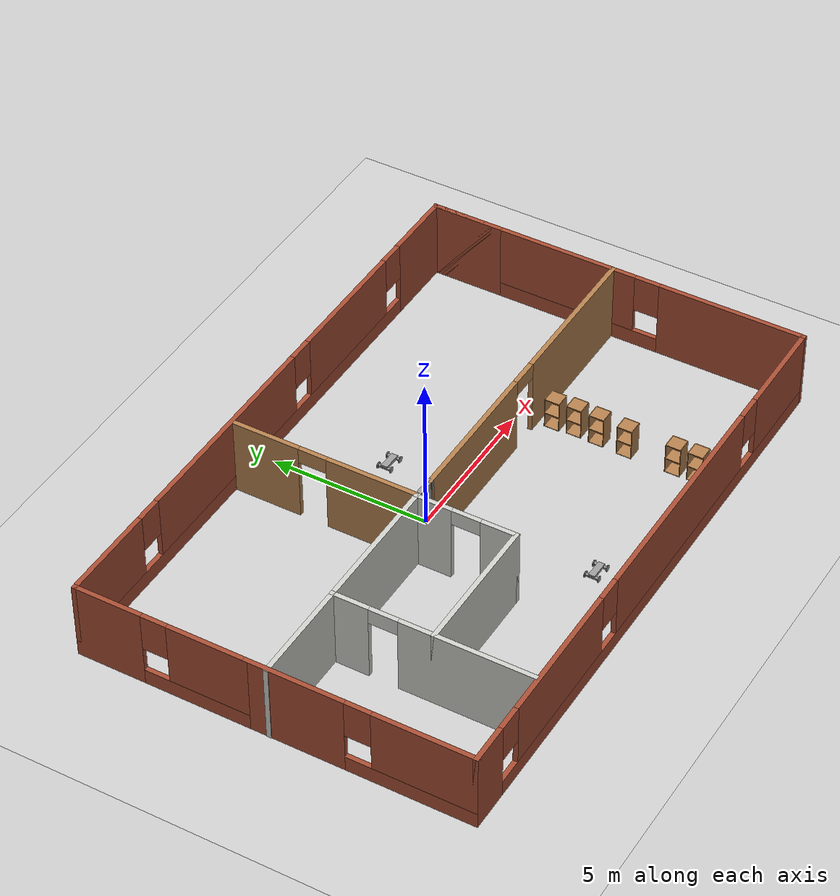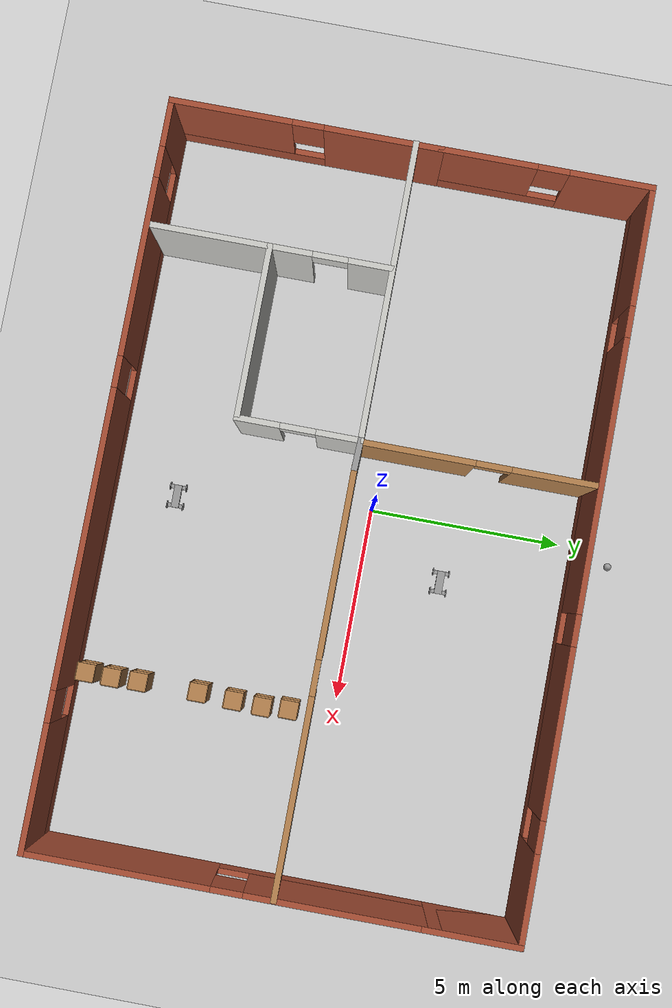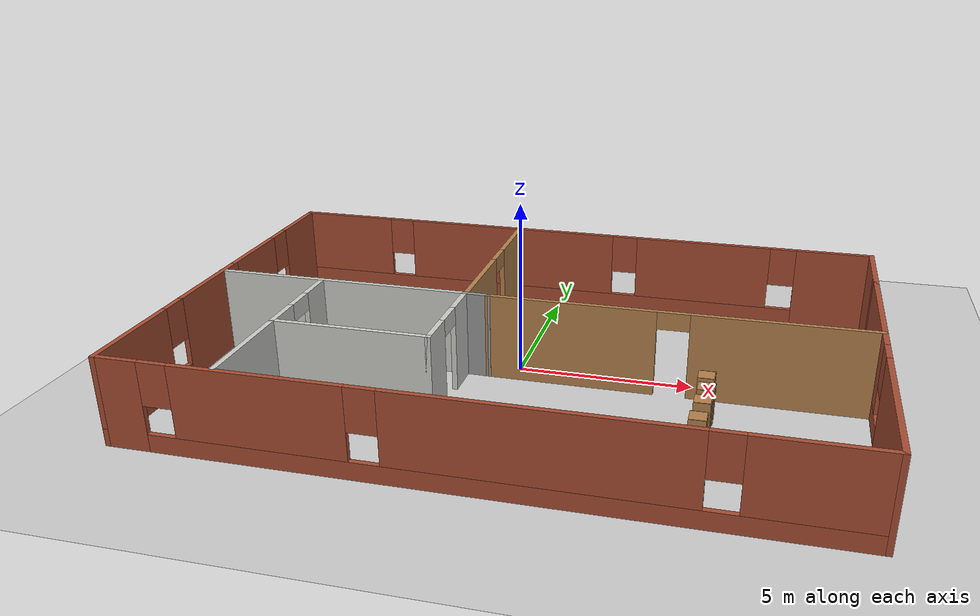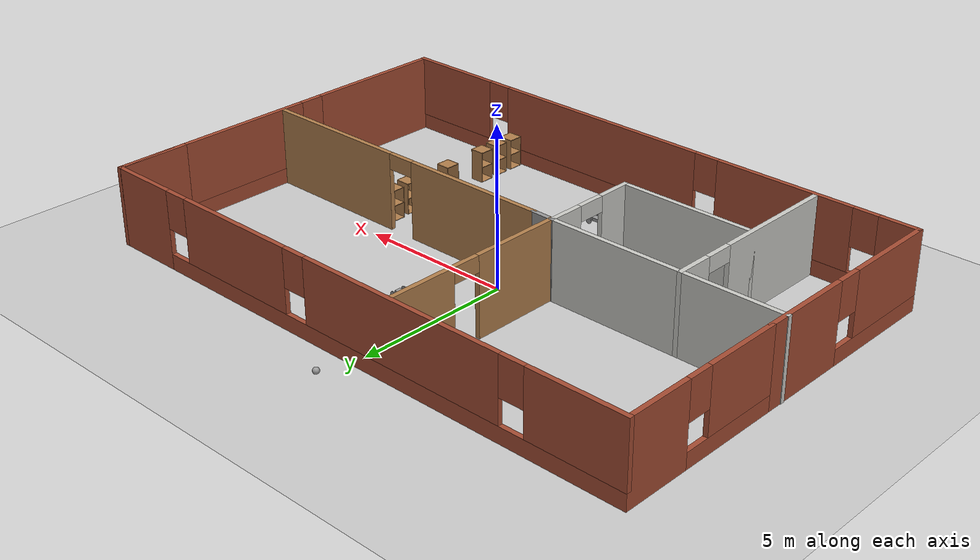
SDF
<sdf version="1.6">
 <world name="default">
  <plugin name="hello" filename="libhello.so"/>
  <light name="sun" type="directional">
   <pose>0 0 10 0 -0 0</pose>
   <diffuse>0.8 0.8 0.8 1</diffuse>
   <specular>0.2 0.2 0.2 1</specular>
   <attenuation>
    <range>1000</range>
    <constant>0.9</constant>
    <linear>0.01</linear>
    <quadratic>0.001</quadratic>
   </attenuation>
   <direction>-0.5 0.1 -0.9</direction>
  </light>
  <model name="ground_plane">
   <static>1</static>
   <link name="link">
    <collision name="collision">
     <geometry><plane><normal>0 0 1</normal><size>100 100</size></plane></geometry>
     <surface>
      <contact><collide_bitmask>65535</collide_bitmask></contact>
      <friction><ode><mu>100</mu><mu2>50</mu2></ode></friction>
     </surface>
    </collision>
    <visual name="visual">
     <cast_shadows>0</cast_shadows>
     <geometry><plane><normal>0 0 1</normal><size>100 100</size></plane></geometry>
     <material>
      <script><uri>file://media/materials/scripts/gazebo.material</uri><name>Gazebo/Grey</name></script>
     </material>
    </visual>
   </link>
  </model>
  <gravity>0 0 -9.8</gravity>
  <magnetic_field>6e-06 2.3e-05 -4.2e-05</magnetic_field>
  <atmosphere type="adiabatic"/>
  <physics name="default_physics" default="0" type="ode">
   <max_step_size>0.001</max_step_size>
   <real_time_factor>1</real_time_factor>
   <real_time_update_rate>1000</real_time_update_rate>
  </physics>
  <scene><ambient>0.4 0.4 0.4 1</ambient><background>0.7 0.7 0.7 1</background><shadows>1</shadows></scene>
  <spherical_coordinates>
   <surface_model>EARTH_WGS84</surface_model>
   <latitude_deg>0</latitude_deg>
   <longitude_deg>0</longitude_deg>
   <elevation>0</elevation>
   <heading_deg>0</heading_deg>
  </spherical_coordinates>
  <model name="Ground_Floor">
   <pose>0.3947 -0.6993 0 0 -0 0</pose>
   <link name="Wall_15">
    <pose>-9.41574 3.425 0 0 0 -1.5708</pose>
    <visual name="Wall_15_Visual_0">
     <pose>-1.66053 0 1.25 0 -0 0</pose>
     <geometry><box><size>2.17893 0.15 2.5</size></box></geometry>
     <material>
      <script><uri>file://media/materials/scripts/gazebo.material</uri><name>Gazebo/Bricks</name></script>
      <ambient>1 1 1 1</ambient>
     </material>
     <meta><layer>0</layer></meta>
    </visual>
    <collision name="Wall_15_Collision_0">
     <geometry><box><size>2.17893 0.15 2.5</size></box></geometry>
     <pose>-1.66053 0 1.25 0 -0 0</pose>
    </collision>
    <visual name="Wall_15_Visual_1">
     <pose>1.08947 0 0.25 0 -0 0</pose>
     <geometry><box><size>3.32107 0.15 0.5</size></box></geometry>
     <material>
      <script><uri>file://media/materials/scripts/gazebo.material</uri><name>Gazebo/Bricks</name></script>
      <ambient>1 1 1 1</ambient>
     </material>
     <meta><layer>0</layer></meta>
    </visual>
    <collision name="Wall_15_Collision_1">
     <geometry><box><size>3.32107 0.15 0.5</size></box></geometry>
     <pose>1.08947 0 0.25 0 -0 0</pose>
    </collision>
    <visual name="Wall_15_Visual_2">
     <pose>1.48947 0 1.5 0 -0 0</pose>
     <geometry><box><size>2.52107 0.15 2</size></box></geometry>
     <material>
      <script><uri>file://media/materials/scripts/gazebo.material</uri><name>Gazebo/Bricks</name></script>
      <ambient>1 1 1 1</ambient>
     </material>
     <meta><layer>0</layer></meta>
    </visual>
    <collision name="Wall_15_Collision_2">
     <geometry><box><size>2.52107 0.15 2</size></box></geometry>
     <pose>1.48947 0 1.5 0 -0 0</pose>
    </collision>
    <visual name="Wall_15_Visual_3">
     <pose>-0.171069 0 1.9 0 -0 0</pose>
     <geometry><box><size>0.8 0.15 1.2</size></box></geometry>
     <material>
      <script><uri>file://media/materials/scripts/gazebo.material</uri><name>Gazebo/Bricks</name></script>
      <ambient>1 1 1 1</ambient>
     </material>
     <meta><layer>0</layer></meta>
    </visual>
    <collision name="Wall_15_Collision_3">
     <geometry><box><size>0.8 0.15 1.2</size></box></geometry>
     <pose>-0.171069 0 1.9 0 -0 0</pose>
    </collision>
   </link>
   <link name="Wall_17">
    <pose>-9.41574 -2.675 0 0 0 -1.5708</pose>
    <visual name="Wall_17_Visual_0">
     <pose>-1.97447 0 1.25 0 -0 0</pose>
     <geometry><box><size>3.05106 0.15 2.5</size></box></geometry>
     <material>
      <script><uri>file://media/materials/scripts/gazebo.material</uri><name>Gazebo/Bricks</name></script>
      <ambient>1 1 1 1</ambient>
     </material>
     <meta><layer>0</layer></meta>
    </visual>
    <collision name="Wall_17_Collision_0">
     <geometry><box><size>3.05106 0.15 2.5</size></box></geometry>
     <pose>-1.97447 0 1.25 0 -0 0</pose>
    </collision>
    <visual name="Wall_17_Visual_1">
     <pose>1.52553 0 0.25 0 -0 0</pose>
     <geometry><box><size>3.94894 0.15 0.5</size></box></geometry>
     <material>
      <script><uri>file://media/materials/scripts/gazebo.material</uri><name>Gazebo/Bricks</name></script>
      <ambient>1 1 1 1</ambient>
     </material>
     <meta><layer>0</layer></meta>
    </visual>
    <collision name="Wall_17_Collision_1">
     <geometry><box><size>3.94894 0.15 0.5</size></box></geometry>
     <pose>1.52553 0 0.25 0 -0 0</pose>
    </collision>
    <visual name="Wall_17_Visual_2">
     <pose>1.92553 0 1.5 0 -0 0</pose>
     <geometry><box><size>3.14894 0.15 2</size></box></geometry>
     <material>
      <script><uri>file://media/materials/scripts/gazebo.material</uri><name>Gazebo/Bricks</name></script>
      <ambient>1 1 1 1</ambient>
     </material>
     <meta><layer>0</layer></meta>
    </visual>
    <collision name="Wall_17_Collision_2">
     <geometry><box><size>3.14894 0.15 2</size></box></geometry>
     <pose>1.92553 0 1.5 0 -0 0</pose>
    </collision>
    <visual name="Wall_17_Visual_3">
     <pose>-0.048936 0 1.9 0 -0 0</pose>
     <geometry><box><size>0.8 0.15 1.2</size></box></geometry>
     <material>
      <script><uri>file://media/materials/scripts/gazebo.material</uri><name>Gazebo/Bricks</name></script>
      <ambient>1 1 1 1</ambient>
     </material>
     <meta><layer>0</layer></meta>
    </visual>
    <collision name="Wall_17_Collision_3">
     <geometry><box><size>0.8 0.15 1.2</size></box></geometry>
     <pose>-0.048936 0 1.9 0 -0 0</pose>
    </collision>
   </link>
   <link name="Wall_18">
    <pose>0.009256 -6.1 0 0 -0 0</pose>
    <visual name="Wall_18_Visual_0">
     <pose>-8.86219 0 1.25 0 -0 0</pose>
     <geometry><box><size>1.27563 0.15 2.5</size></box></geometry>
     <material>
      <script><uri>file://media/materials/scripts/gazebo.material</uri><name>Gazebo/Bricks</name></script>
      <ambient>1 1 1 1</ambient>
     </material>
     <meta><layer>0</layer></meta>
    </visual>
    <collision name="Wall_18_Collision_0">
     <geometry><box><size>1.27563 0.15 2.5</size></box></geometry>
     <pose>-8.86219 0 1.25 0 -0 0</pose>
    </collision>
    <visual name="Wall_18_Visual_1">
     <pose>0.637815 0 0.25 0 -0 0</pose>
     <geometry><box><size>17.7244 0.15 0.5</size></box></geometry>
     <material>
      <script><uri>file://media/materials/scripts/gazebo.material</uri><name>Gazebo/Bricks</name></script>
      <ambient>1 1 1 1</ambient>
     </material>
     <meta><layer>0</layer></meta>
    </visual>
    <collision name="Wall_18_Collision_1">
     <geometry><box><size>17.7244 0.15 0.5</size></box></geometry>
     <pose>0.637815 0 0.25 0 -0 0</pose>
    </collision>
    <visual name="Wall_18_Visual_2">
     <pose>-5.14122 0 1.5 0 -0 0</pose>
     <geometry><box><size>4.5663 0.15 2</size></box></geometry>
     <material>
      <script><uri>file://media/materials/scripts/gazebo.material</uri><name>Gazebo/Bricks</name></script>
      <ambient>1 1 1 1</ambient>
     </material>
     <meta><layer>0</layer></meta>
    </visual>
    <collision name="Wall_18_Collision_2">
     <geometry><box><size>4.5663 0.15 2</size></box></geometry>
     <pose>-5.14122 0 1.5 0 -0 0</pose>
    </collision>
    <visual name="Wall_18_Visual_3">
     <pose>1.70544 0 1.5 0 -0 0</pose>
     <geometry><box><size>7.52702 0.15 2</size></box></geometry>
     <material>
      <script><uri>file://media/materials/scripts/gazebo.material</uri><name>Gazebo/Bricks</name></script>
      <ambient>1 1 1 1</ambient>
     </material>
     <meta><layer>0</layer></meta>
    </visual>
    <collision name="Wall_18_Collision_3">
     <geometry><box><size>7.52702 0.15 2</size></box></geometry>
     <pose>1.70544 0 1.5 0 -0 0</pose>
    </collision>
    <visual name="Wall_18_Visual_4">
     <pose>7.88448 0 1.5 0 -0 0</pose>
     <geometry><box><size>3.23105 0.15 2</size></box></geometry>
     <material>
      <script><uri>file://media/materials/scripts/gazebo.material</uri><name>Gazebo/Bricks</name></script>
      <ambient>1 1 1 1</ambient>
     </material>
     <meta><layer>0</layer></meta>
    </visual>
    <collision name="Wall_18_Collision_4">
     <geometry><box><size>3.23105 0.15 2</size></box></geometry>
     <pose>7.88448 0 1.5 0 -0 0</pose>
    </collision>
    <visual name="Wall_18_Visual_5">
     <pose>-7.82437 0 1.9 0 -0 0</pose>
     <geometry><box><size>0.8 0.15 1.2</size></box></geometry>
     <material>
      <script><uri>file://media/materials/scripts/gazebo.material</uri><name>Gazebo/Bricks</name></script>
      <ambient>1 1 1 1</ambient>
     </material>
     <meta><layer>0</layer></meta>
    </visual>
    <collision name="Wall_18_Collision_5">
     <geometry><box><size>0.8 0.15 1.2</size></box></geometry>
     <pose>-7.82437 0 1.9 0 -0 0</pose>
    </collision>
    <visual name="Wall_18_Visual_6">
     <pose>-2.45807 0 1.9 0 -0 0</pose>
     <geometry><box><size>0.8 0.15 1.2</size></box></geometry>
     <material>
      <script><uri>file://media/materials/scripts/gazebo.material</uri><name>Gazebo/Bricks</name></script>
      <ambient>1 1 1 1</ambient>
     </material>
     <meta><layer>0</layer></meta>
    </visual>
    <collision name="Wall_18_Collision_6">
     <geometry><box><size>0.8 0.15 1.2</size></box></geometry>
     <pose>-2.45807 0 1.9 0 -0 0</pose>
    </collision>
    <visual name="Wall_18_Visual_7">
     <pose>5.86895 0 1.9 0 -0 0</pose>
     <geometry><box><size>0.8 0.15 1.2</size></box></geometry>
     <material>
      <script><uri>file://media/materials/scripts/gazebo.material</uri><name>Gazebo/Bricks</name></script>
      <ambient>1 1 1 1</ambient>
     </material>
     <meta><layer>0</layer></meta>
    </visual>
    <collision name="Wall_18_Collision_7">
     <geometry><box><size>0.8 0.15 1.2</size></box></geometry>
     <pose>5.86895 0 1.9 0 -0 0</pose>
    </collision>
   </link>
   <link name="Wall_19">
    <pose>9.43426 -1.175 0 0 -0 1.5708</pose>
    <visual name="Wall_19_Visual_0">
     <pose>-2.65066 0 1.25 0 -0 0</pose>
     <geometry><box><size>4.69869 0.15 2.5</size></box></geometry>
     <material>
      <script><uri>file://media/materials/scripts/gazebo.material</uri><name>Gazebo/Bricks</name></script>
      <ambient>1 1 1 1</ambient>
     </material>
     <meta><layer>0</layer></meta>
    </visual>
    <collision name="Wall_19_Collision_0">
     <geometry><box><size>4.69869 0.15 2.5</size></box></geometry>
     <pose>-2.65066 0 1.25 0 -0 0</pose>
    </collision>
    <visual name="Wall_19_Visual_1">
     <pose>2.34934 0 0.25 0 -0 0</pose>
     <geometry><box><size>5.30131 0.15 0.5</size></box></geometry>
     <material>
      <script><uri>file://media/materials/scripts/gazebo.material</uri><name>Gazebo/Bricks</name></script>
      <ambient>1 1 1 1</ambient>
     </material>
     <meta><layer>0</layer></meta>
    </visual>
    <collision name="Wall_19_Collision_1">
     <geometry><box><size>5.30131 0.15 0.5</size></box></geometry>
     <pose>2.34934 0 0.25 0 -0 0</pose>
    </collision>
    <visual name="Wall_19_Visual_2">
     <pose>2.74934 0 1.5 0 -0 0</pose>
     <geometry><box><size>4.50131 0.15 2</size></box></geometry>
     <material>
      <script><uri>file://media/materials/scripts/gazebo.material</uri><name>Gazebo/Bricks</name></script>
      <ambient>1 1 1 1</ambient>
     </material>
     <meta><layer>0</layer></meta>
    </visual>
    <collision name="Wall_19_Collision_2">
     <geometry><box><size>4.50131 0.15 2</size></box></geometry>
     <pose>2.74934 0 1.5 0 -0 0</pose>
    </collision>
    <visual name="Wall_19_Visual_3">
     <pose>0.098686 0 1.9 0 -0 0</pose>
     <geometry><box><size>0.8 0.15 1.2</size></box></geometry>
     <material>
      <script><uri>file://media/materials/scripts/gazebo.material</uri><name>Gazebo/Bricks</name></script>
      <ambient>1 1 1 1</ambient>
     </material>
     <meta><layer>0</layer></meta>
    </visual>
    <collision name="Wall_19_Collision_3">
     <geometry><box><size>0.8 0.15 1.2</size></box></geometry>
     <pose>0.098686 0 1.9 0 -0 0</pose>
    </collision>
   </link>
   <link name="Wall_21">
    <pose>9.43426 4.925 0 0 -0 1.5708</pose>
    <visual name="Wall_21_Visual_0">
     <pose>0 0 1.25 0 -0 0</pose>
     <geometry><box><size>2.5 0.15 2.5</size></box></geometry>
     <material>
      <script><uri>file://media/materials/scripts/gazebo.material</uri><name>Gazebo/Bricks</name></script>
      <ambient>1 1 1 1</ambient>
     </material>
     <meta><layer>0</layer></meta>
    </visual>
    <collision name="Wall_21_Collision_0">
     <geometry><box><size>2.5 0.15 2.5</size></box></geometry>
     <pose>0 0 1.25 0 -0 0</pose>
    </collision>
    <visual name="Wall_21_Visual_1">
     <pose>0.243361 0 1.25 0 -0 0</pose>
     <geometry><box><size>2.01328 0.15 2.5</size></box></geometry>
     <material>
      <script><uri>file://media/materials/scripts/gazebo.material</uri><name>Gazebo/Bricks</name></script>
      <ambient>1 1 1 1</ambient>
     </material>
     <meta><layer>0</layer></meta>
    </visual>
    <collision name="Wall_21_Collision_1">
     <geometry><box><size>2.01328 0.15 2.5</size></box></geometry>
     <pose>0.243361 0 1.25 0 -0 0</pose>
    </collision>
   </link>
   <link name="Wall_22">
    <pose>0.009256 6.1 0 0 -0 3.14159</pose>
    <visual name="Wall_22_Visual_0">
     <pose>-8.33552 0 1.25 0 -0 0</pose>
     <geometry><box><size>2.32896 0.15 2.5</size></box></geometry>
     <material>
      <script><uri>file://media/materials/scripts/gazebo.material</uri><name>Gazebo/Bricks</name></script>
      <ambient>1 1 1 1</ambient>
     </material>
     <meta><layer>0</layer></meta>
    </visual>
    <collision name="Wall_22_Collision_0">
     <geometry><box><size>2.32896 0.15 2.5</size></box></geometry>
     <pose>-8.33552 0 1.25 0 -0 0</pose>
    </collision>
    <visual name="Wall_22_Visual_1">
     <pose>1.16448 0 0.25 0 -0 0</pose>
     <geometry><box><size>16.671 0.15 0.5</size></box></geometry>
     <material>
      <script><uri>file://media/materials/scripts/gazebo.material</uri><name>Gazebo/Bricks</name></script>
      <ambient>1 1 1 1</ambient>
     </material>
     <meta><layer>0</layer></meta>
    </visual>
    <collision name="Wall_22_Collision_1">
     <geometry><box><size>16.671 0.15 0.5</size></box></geometry>
     <pose>1.16448 0 0.25 0 -0 0</pose>
    </collision>
    <visual name="Wall_22_Visual_2">
     <pose>-4.24981 0 1.5 0 -0 0</pose>
     <geometry><box><size>4.24247 0.15 2</size></box></geometry>
     <material>
      <script><uri>file://media/materials/scripts/gazebo.material</uri><name>Gazebo/Bricks</name></script>
      <ambient>1 1 1 1</ambient>
     </material>
     <meta><layer>0</layer></meta>
    </visual>
    <collision name="Wall_22_Collision_2">
     <geometry><box><size>4.24247 0.15 2</size></box></geometry>
     <pose>-4.24981 0 1.5 0 -0 0</pose>
    </collision>
    <visual name="Wall_22_Visual_3">
     <pose>2.13424 0 1.5 0 -0 0</pose>
     <geometry><box><size>6.92562 0.15 2</size></box></geometry>
     <material>
      <script><uri>file://media/materials/scripts/gazebo.material</uri><name>Gazebo/Bricks</name></script>
      <ambient>1 1 1 1</ambient>
     </material>
     <meta><layer>0</layer></meta>
    </visual>
    <collision name="Wall_22_Collision_3">
     <geometry><box><size>6.92562 0.15 2</size></box></geometry>
     <pose>2.13424 0 1.5 0 -0 0</pose>
    </collision>
    <visual name="Wall_22_Visual_4">
     <pose>7.94853 0 1.5 0 -0 0</pose>
     <geometry><box><size>3.10295 0.15 2</size></box></geometry>
     <material>
      <script><uri>file://media/materials/scripts/gazebo.material</uri><name>Gazebo/Bricks</name></script>
      <ambient>1 1 1 1</ambient>
     </material>
     <meta><layer>0</layer></meta>
    </visual>
    <collision name="Wall_22_Collision_4">
     <geometry><box><size>3.10295 0.15 2</size></box></geometry>
     <pose>7.94853 0 1.5 0 -0 0</pose>
    </collision>
    <visual name="Wall_22_Visual_5">
     <pose>-6.77104 0 1.9 0 -0 0</pose>
     <geometry><box><size>0.8 0.15 1.2</size></box></geometry>
     <material>
      <script><uri>file://media/materials/scripts/gazebo.material</uri><name>Gazebo/Bricks</name></script>
      <ambient>1 1 1 1</ambient>
     </material>
     <meta><layer>0</layer></meta>
    </visual>
    <collision name="Wall_22_Collision_5">
     <geometry><box><size>0.8 0.15 1.2</size></box></geometry>
     <pose>-6.77104 0 1.9 0 -0 0</pose>
    </collision>
    <visual name="Wall_22_Visual_6">
     <pose>-1.72857 0 1.9 0 -0 0</pose>
     <geometry><box><size>0.8 0.15 1.2</size></box></geometry>
     <material>
      <script><uri>file://media/materials/scripts/gazebo.material</uri><name>Gazebo/Bricks</name></script>
      <ambient>1 1 1 1</ambient>
     </material>
     <meta><layer>0</layer></meta>
    </visual>
    <collision name="Wall_22_Collision_6">
     <geometry><box><size>0.8 0.15 1.2</size></box></geometry>
     <pose>-1.72857 0 1.9 0 -0 0</pose>
    </collision>
    <visual name="Wall_22_Visual_7">
     <pose>5.99705 0 1.9 0 -0 0</pose>
     <geometry><box><size>0.8 0.15 1.2</size></box></geometry>
     <material>
      <script><uri>file://media/materials/scripts/gazebo.material</uri><name>Gazebo/Bricks</name></script>
      <ambient>1 1 1 1</ambient>
     </material>
     <meta><layer>0</layer></meta>
    </visual>
    <collision name="Wall_22_Collision_7">
     <geometry><box><size>0.8 0.15 1.2</size></box></geometry>
     <pose>5.99705 0 1.9 0 -0 0</pose>
    </collision>
   </link>
   <link name="Wall_24">
    <collision name="Wall_24_Collision">
     <geometry><box><size>7.75 0.15 2.5</size></box></geometry>
     <pose>0 0 1.25 0 -0 0</pose>
    </collision>
    <visual name="Wall_24_Visual">
     <pose>0 0 1.25 0 -0 0</pose>
     <geometry><box><size>7.75 0.15 2.5</size></box></geometry>
     <material>
      <script><uri>file://media/materials/scripts/gazebo.material</uri><name>Gazebo/CeilingTiled</name></script>
      <ambient>1 1 1 1</ambient>
     </material>
     <meta><layer>0</layer></meta>
    </visual>
    <pose>-5.63426 0.103347 0 0 -0 0</pose>
   </link>
   <link name="Wall_25">
    <pose>-1.83426 3.02835 0 0 -0 1.5708</pose>
    <visual name="Wall_25_Visual_0">
     <pose>-1.5221 0 1.25 0 -0 0</pose>
     <geometry><box><size>2.95581 0.15 2.5</size></box></geometry>
     <material>
      <script><uri>file://media/materials/scripts/gazebo.material</uri><name>Gazebo/Wood</name></script>
      <ambient>1 1 1 1</ambient>
     </material>
     <meta><layer>0</layer></meta>
    </visual>
    <collision name="Wall_25_Collision_0">
     <geometry><box><size>2.95581 0.15 2.5</size></box></geometry>
     <pose>-1.5221 0 1.25 0 -0 0</pose>
    </collision>
    <visual name="Wall_25_Visual_1">
     <pose>1.9279 0 1.25 0 -0 0</pose>
     <geometry><box><size>2.14419 0.15 2.5</size></box></geometry>
     <material>
      <script><uri>file://media/materials/scripts/gazebo.material</uri><name>Gazebo/Wood</name></script>
      <ambient>1 1 1 1</ambient>
     </material>
     <meta><layer>0</layer></meta>
    </visual>
    <collision name="Wall_25_Collision_1">
     <geometry><box><size>2.14419 0.15 2.5</size></box></geometry>
     <pose>1.9279 0 1.25 0 -0 0</pose>
    </collision>
    <visual name="Wall_25_Visual_2">
     <pose>0.405807 0 2.25 0 -0 0</pose>
     <geometry><box><size>0.9 0.15 0.5</size></box></geometry>
     <material>
      <script><uri>file://media/materials/scripts/gazebo.material</uri><name>Gazebo/Wood</name></script>
      <ambient>1 1 1 1</ambient>
     </material>
     <meta><layer>0</layer></meta>
    </visual>
    <collision name="Wall_25_Collision_2">
     <geometry><box><size>0.9 0.15 0.5</size></box></geometry>
     <pose>0.405807 0 2.25 0 -0 0</pose>
    </collision>
   </link>
   <link name="Wall_27">
    <pose>-6.2191 -2.94665 0 0 0 -1.5708</pose>
    <visual name="Wall_27_Visual_0">
     <pose>-2.52606 0 1.25 0 -0 0</pose>
     <geometry><box><size>1.19788 0.15 2.5</size></box></geometry>
     <material>
      <script><uri>file://media/materials/scripts/gazebo.material</uri><name>Gazebo/CeilingTiled</name></script>
      <ambient>1 1 1 1</ambient>
     </material>
     <meta><layer>0</layer></meta>
    </visual>
    <collision name="Wall_27_Collision_0">
     <geometry><box><size>1.19788 0.15 2.5</size></box></geometry>
     <pose>-2.52606 0 1.25 0 -0 0</pose>
    </collision>
    <visual name="Wall_27_Visual_1">
     <pose>1.04894 0 1.25 0 -0 0</pose>
     <geometry><box><size>4.15212 0.15 2.5</size></box></geometry>
     <material>
      <script><uri>file://media/materials/scripts/gazebo.material</uri><name>Gazebo/CeilingTiled</name></script>
      <ambient>1 1 1 1</ambient>
     </material>
     <meta><layer>0</layer></meta>
    </visual>
    <collision name="Wall_27_Collision_1">
     <geometry><box><size>4.15212 0.15 2.5</size></box></geometry>
     <pose>1.04894 0 1.25 0 -0 0</pose>
    </collision>
    <visual name="Wall_27_Visual_2">
     <pose>-1.47712 0 2.25 0 -0 0</pose>
     <geometry><box><size>0.9 0.15 0.5</size></box></geometry>
     <material>
      <script><uri>file://media/materials/scripts/gazebo.material</uri><name>Gazebo/CeilingTiled</name></script>
      <ambient>1 1 1 1</ambient>
     </material>
     <meta><layer>0</layer></meta>
    </visual>
    <collision name="Wall_27_Collision_2">
     <geometry><box><size>0.9 0.15 0.5</size></box></geometry>
     <pose>-1.47712 0 2.25 0 -0 0</pose>
    </collision>
   </link>
   <link name="Wall_29">
    <collision name="Wall_29_Collision">
     <geometry><box><size>4.5 0.15 2.5</size></box></geometry>
     <pose>0 0 1.25 0 -0 0</pose>
    </collision>
    <visual name="Wall_29_Visual">
     <pose>0 0 1.25 0 -0 0</pose>
     <geometry><box><size>4.5 0.15 2.5</size></box></geometry>
     <material>
      <script><uri>file://media/materials/scripts/gazebo.material</uri><name>Gazebo/CeilingTiled</name></script>
      <ambient>1 1 1 1</ambient>
     </material>
     <meta><layer>0</layer></meta>
    </visual>
    <pose>-4.0441 -2.99615 0 0 -0 0</pose>
   </link>
   <link name="Wall_30">
    <pose>-1.8691 -1.44615 0 0 -0 1.5708</pose>
    <visual name="Wall_30_Visual_0">
     <pose>-1.04919 0 1.25 0 -0 0</pose>
     <geometry><box><size>1.15162 0.15 2.5</size></box></geometry>
     <material>
      <script><uri>file://media/materials/scripts/gazebo.material</uri><name>Gazebo/CeilingTiled</name></script>
      <ambient>1 1 1 1</ambient>
     </material>
     <meta><layer>0</layer></meta>
    </visual>
    <collision name="Wall_30_Collision_0">
     <geometry><box><size>1.15162 0.15 2.5</size></box></geometry>
     <pose>-1.04919 0 1.25 0 -0 0</pose>
    </collision>
    <visual name="Wall_30_Visual_1">
     <pose>1.02581 0 1.25 0 -0 0</pose>
     <geometry><box><size>1.19838 0.15 2.5</size></box></geometry>
     <material>
      <script><uri>file://media/materials/scripts/gazebo.material</uri><name>Gazebo/CeilingTiled</name></script>
      <ambient>1 1 1 1</ambient>
     </material>
     <meta><layer>0</layer></meta>
    </visual>
    <collision name="Wall_30_Collision_1">
     <geometry><box><size>1.19838 0.15 2.5</size></box></geometry>
     <pose>1.02581 0 1.25 0 -0 0</pose>
    </collision>
    <visual name="Wall_30_Visual_2">
     <pose>-0.02338 0 2.25 0 -0 0</pose>
     <geometry><box><size>0.9 0.15 0.5</size></box></geometry>
     <material>
      <script><uri>file://media/materials/scripts/gazebo.material</uri><name>Gazebo/CeilingTiled</name></script>
      <ambient>1 1 1 1</ambient>
     </material>
     <meta><layer>0</layer></meta>
    </visual>
    <collision name="Wall_30_Collision_2">
     <geometry><box><size>0.9 0.15 0.5</size></box></geometry>
     <pose>-0.02338 0 2.25 0 -0 0</pose>
    </collision>
   </link>
   <link name="Wall_32">
    <pose>4.11719 0.080217 0 0 -0 3.14159</pose>
    <visual name="Wall_32_Visual_0">
     <pose>-2.86778 0 1.25 0 -0 0</pose>
     <geometry><box><size>5.01443 0.15 2.5</size></box></geometry>
     <material>
      <script><uri>file://media/materials/scripts/gazebo.material</uri><name>Gazebo/Wood</name></script>
      <ambient>1 1 1 1</ambient>
     </material>
     <meta><layer>0</layer></meta>
    </visual>
    <collision name="Wall_32_Collision_0">
     <geometry><box><size>5.01443 0.15 2.5</size></box></geometry>
     <pose>-2.86778 0 1.25 0 -0 0</pose>
    </collision>
    <visual name="Wall_32_Visual_1">
     <pose>2.95722 0 1.25 0 -0 0</pose>
     <geometry><box><size>4.83557 0.15 2.5</size></box></geometry>
     <material>
      <script><uri>file://media/materials/scripts/gazebo.material</uri><name>Gazebo/Wood</name></script>
      <ambient>1 1 1 1</ambient>
     </material>
     <meta><layer>0</layer></meta>
    </visual>
    <collision name="Wall_32_Collision_1">
     <geometry><box><size>4.83557 0.15 2.5</size></box></geometry>
     <pose>2.95722 0 1.25 0 -0 0</pose>
    </collision>
    <visual name="Wall_32_Visual_2">
     <pose>0.089432 0 2.25 0 -0 0</pose>
     <geometry><box><size>0.9 0.15 0.5</size></box></geometry>
     <material>
      <script><uri>file://media/materials/scripts/gazebo.material</uri><name>Gazebo/Wood</name></script>
      <ambient>1 1 1 1</ambient>
     </material>
     <meta><layer>0</layer></meta>
    </visual>
    <collision name="Wall_32_Collision_2">
     <geometry><box><size>0.9 0.15 0.5</size></box></geometry>
     <pose>0.089432 0 2.25 0 -0 0</pose>
    </collision>
   </link>
   <link name="Wall_33">
    <collision name="Wall_33_Collision">
     <geometry><box><size>0.836697 0.15 2.5</size></box></geometry>
     <pose>0 0 1.25 0 -0 0</pose>
    </collision>
    <visual name="Wall_33_Visual">
     <pose>0 0 1.25 0 -0 0</pose>
     <geometry><box><size>0.836697 0.15 2.5</size></box></geometry>
     <material>
      <script><uri>file://media/materials/scripts/gazebo.material</uri><name>Gazebo/Grey</name></script>
      <ambient>1 1 1 1</ambient>
     </material>
     <meta><layer>0</layer></meta>
    </visual>
    <pose>-1.52596 0.092031 0 0 -0 3.10718</pose>
   </link>
   <static>1</static>
  </model>
  <model name="Four_Wheel_Model">
   <link name="link_0">
    <pose>0 0 0.2 -6e-06 -0 1.5e-05</pose>
    <inertial>
     <mass>1</mass>
     <inertia>
      <ixx>0.166667</ixx>
      <ixy>0</ixy>
      <ixz>0</ixz>
      <iyy>0.166667</iyy>
      <iyz>0</iyz>
      <izz>0.166667</izz>
     </inertia>
    </inertial>
    <visual name="visual">
     <geometry><box><size>0.6 0.2 0.1</size></box></geometry>
     <material>
      <lighting>1</lighting>
      <script><uri>file://media/materials/scripts/gazebo.material</uri><name>Gazebo/Grey</name></script>
      <ambient>0.3 0.3 0.3 1</ambient>
      <diffuse>0.7 0.7 0.7 1</diffuse>
      <specular>0.01 0.01 0.01 1</specular>
      <emissive>0 0 0 1</emissive>
      <shader type="vertex"><normal_map>__default__</normal_map></shader>
     </material>
    </visual>
    <collision name="collision">
     <geometry><box><size>0.6 0.2 0.1</size></box></geometry>
     <surface>
      <friction>
       <ode><mu>1</mu><mu2>1</mu2><fdir1>0 0 0</fdir1><slip1>0</slip1><slip2>0</slip2></ode>
       <torsional>
        <coefficient>1</coefficient>
        <patch_radius>0</patch_radius>
        <surface_radius>0</surface_radius>
        <use_patch_radius>1</use_patch_radius>
        <ode><slip>0</slip></ode>
       </torsional>
      </friction>
      <bounce><restitution_coefficient>0</restitution_coefficient><threshold>1e+06</threshold></bounce>
      <contact>
       <collide_without_contact>0</collide_without_contact>
       <collide_without_contact_bitmask>1</collide_without_contact_bitmask>
       <collide_bitmask>1</collide_bitmask>
       <ode>
        <soft_cfm>0</soft_cfm>
        <soft_erp>0.2</soft_erp>
        <kp>1e+13</kp>
        <kd>1</kd>
        <max_vel>0.01</max_vel>
        <min_depth>0</min_depth>
       </ode>
       <bullet>
        <split_impulse>1</split_impulse>
        <split_impulse_penetration_threshold>-0.01</split_impulse_penetration_threshold>
        <soft_cfm>0</soft_cfm>
        <soft_erp>0.2</soft_erp>
        <kp>1e+13</kp>
        <kd>1</kd>
       </bullet>
      </contact>
     </surface>
    </collision>
   </link>
   <link name="link_0_0">
    <pose>-0.250001 0 0.162322 -6e-06 0 0</pose>
    <inertial>
     <mass>1</mass>
     <inertia>
      <ixx>0.166667</ixx>
      <ixy>0</ixy>
      <ixz>0</ixz>
      <iyy>0.166667</iyy>
      <iyz>0</iyz>
      <izz>0.166667</izz>
     </inertia>
    </inertial>
    <visual name="visual">
     <geometry><box><size>0.1 0.4 0.05</size></box></geometry>
     <material>
      <lighting>1</lighting>
      <script><uri>file://media/materials/scripts/gazebo.material</uri><name>Gazebo/Grey</name></script>
      <shader type="pixel"><normal_map>__default__</normal_map></shader>
      <ambient>0.3 0.3 0.3 1</ambient>
      <diffuse>0.7 0.7 0.7 1</diffuse>
      <specular>0.01 0.01 0.01 1</specular>
      <emissive>0 0 0 1</emissive>
     </material>
    </visual>
    <collision name="collision">
     <geometry><box><size>0.1 0.4 0.05</size></box></geometry>
     <surface>
      <friction>
       <ode><mu>1</mu><mu2>1</mu2><fdir1>0 0 0</fdir1><slip1>0</slip1><slip2>0</slip2></ode>
       <torsional>
        <coefficient>1</coefficient>
        <patch_radius>0</patch_radius>
        <surface_radius>0</surface_radius>
        <use_patch_radius>1</use_patch_radius>
        <ode><slip>0</slip></ode>
       </torsional>
      </friction>
      <bounce><restitution_coefficient>0</restitution_coefficient><threshold>1e+06</threshold></bounce>
      <contact>
       <collide_without_contact>0</collide_without_contact>
       <collide_without_contact_bitmask>1</collide_without_contact_bitmask>
       <collide_bitmask>1</collide_bitmask>
       <ode>
        <soft_cfm>0</soft_cfm>
        <soft_erp>0.2</soft_erp>
        <kp>1e+13</kp>
        <kd>1</kd>
        <max_vel>0.01</max_vel>
        <min_depth>0</min_depth>
       </ode>
       <bullet>
        <split_impulse>1</split_impulse>
        <split_impulse_penetration_threshold>-0.01</split_impulse_penetration_threshold>
        <soft_cfm>0</soft_cfm>
        <soft_erp>0.2</soft_erp>
        <kp>1e+13</kp>
        <kd>1</kd>
       </bullet>
      </contact>
     </surface>
    </collision>
   </link>
   <link name="link_0_clone_clone">
    <pose>0.249959 4e-06 0.175 -0 6e-06 1.57102</pose>
    <inertial>
     <mass>1</mass>
     <inertia>
      <ixx>0.166667</ixx>
      <ixy>0</ixy>
      <ixz>0</ixz>
      <iyy>0.166667</iyy>
      <iyz>0</iyz>
      <izz>0.166667</izz>
     </inertia>
    </inertial>
    <visual name="visual">
     <geometry><box><size>0.4 0.1 0.05</size></box></geometry>
     <material>
      <lighting>1</lighting>
      <script><uri>file://media/materials/scripts/gazebo.material</uri><name>Gazebo/Grey</name></script>
      <ambient>0.3 0.3 0.3 1</ambient>
      <diffuse>0.7 0.7 0.7 1</diffuse>
      <specular>0.01 0.01 0.01 1</specular>
      <emissive>0 0 0 1</emissive>
      <shader type="vertex"><normal_map>__default__</normal_map></shader>
     </material>
    </visual>
    <collision name="collision">
     <geometry><box><size>0.4 0.1 0.05</size></box></geometry>
     <surface>
      <friction>
       <ode><mu>1</mu><mu2>1</mu2><fdir1>0 0 0</fdir1><slip1>0</slip1><slip2>0</slip2></ode>
       <torsional>
        <coefficient>1</coefficient>
        <patch_radius>0</patch_radius>
        <surface_radius>0</surface_radius>
        <use_patch_radius>1</use_patch_radius>
        <ode><slip>0</slip></ode>
       </torsional>
      </friction>
      <bounce><restitution_coefficient>0</restitution_coefficient><threshold>1e+06</threshold></bounce>
      <contact>
       <collide_without_contact>0</collide_without_contact>
       <collide_without_contact_bitmask>1</collide_without_contact_bitmask>
       <collide_bitmask>1</collide_bitmask>
       <ode>
        <soft_cfm>0</soft_cfm>
        <soft_erp>0.2</soft_erp>
        <kp>1e+13</kp>
        <kd>1</kd>
        <max_vel>0.01</max_vel>
        <min_depth>0</min_depth>
       </ode>
       <bullet>
        <split_impulse>1</split_impulse>
        <split_impulse_penetration_threshold>-0.01</split_impulse_penetration_threshold>
        <soft_cfm>0</soft_cfm>
        <soft_erp>0.2</soft_erp>
        <kp>1e+13</kp>
        <kd>1</kd>
       </bullet>
      </contact>
     </surface>
    </collision>
   </link>
   <link name="link_1">
    <pose>0.250006 -0.209996 0.175001 -1.57012 1.57059 -3.14111</pose>
    <inertial>
     <mass>1</mass>
     <inertia><ixx>0.145833</ixx><ixy>0</ixy><ixz>0</ixz><iyy>0.145833</iyy><iyz>0</iyz><izz>0.125</izz></inertia>
    </inertial>
    <visual name="visual">
     <geometry><cylinder><radius>0.1</radius><length>0.025</length></cylinder></geometry>
     <material>
      <lighting>1</lighting>
      <script><uri>file://media/materials/scripts/gazebo.material</uri><name>Gazebo/Grey</name></script>
      <shader type="pixel"><normal_map>__default__</normal_map></shader>
      <ambient>0.3 0.3 0.3 1</ambient>
      <diffuse>0.7 0.7 0.7 1</diffuse>
      <specular>0.01 0.01 0.01 1</specular>
      <emissive>0 0 0 1</emissive>
     </material>
    </visual>
    <collision name="collision">
     <geometry><cylinder><radius>0.1</radius><length>0.025</length></cylinder></geometry>
     <surface>
      <friction>
       <ode><mu>1</mu><mu2>1</mu2><fdir1>0 0 0</fdir1><slip1>0</slip1><slip2>0</slip2></ode>
       <torsional>
        <coefficient>1</coefficient>
        <patch_radius>0</patch_radius>
        <surface_radius>0</surface_radius>
        <use_patch_radius>1</use_patch_radius>
        <ode><slip>0</slip></ode>
       </torsional>
      </friction>
      <bounce><restitution_coefficient>0</restitution_coefficient><threshold>1e+06</threshold></bounce>
      <contact>
       <collide_without_contact>0</collide_without_contact>
       <collide_without_contact_bitmask>1</collide_without_contact_bitmask>
       <collide_bitmask>1</collide_bitmask>
       <ode>
        <soft_cfm>0</soft_cfm>
        <soft_erp>0.2</soft_erp>
        <kp>1e+13</kp>
        <kd>1</kd>
        <max_vel>0.01</max_vel>
        <min_depth>0</min_depth>
       </ode>
       <bullet>
        <split_impulse>1</split_impulse>
        <split_impulse_penetration_threshold>-0.01</split_impulse_penetration_threshold>
        <soft_cfm>0</soft_cfm>
        <soft_erp>0.2</soft_erp>
        <kp>1e+13</kp>
        <kd>1</kd>
       </bullet>
      </contact>
     </surface>
    </collision>
   </link>
   <link name="link_1_0">
    <pose>0.249912 0.210004 0.174999 -1.5707 1.57059 3.14149</pose>
    <inertial>
     <mass>1</mass>
     <inertia><ixx>0.145833</ixx><ixy>0</ixy><ixz>0</ixz><iyy>0.145833</iyy><iyz>0</iyz><izz>0.125</izz></inertia>
    </inertial>
    <visual name="visual">
     <geometry><cylinder><radius>0.1</radius><length>0.025</length></cylinder></geometry>
     <material>
      <lighting>1</lighting>
      <script><uri>file://media/materials/scripts/gazebo.material</uri><name>Gazebo/Grey</name></script>
      <shader type="pixel"><normal_map>__default__</normal_map></shader>
      <ambient>0.3 0.3 0.3 1</ambient>
      <diffuse>0.7 0.7 0.7 1</diffuse>
      <specular>0.01 0.01 0.01 1</specular>
      <emissive>0 0 0 1</emissive>
     </material>
    </visual>
    <collision name="collision">
     <geometry><cylinder><radius>0.1</radius><length>0.025</length></cylinder></geometry>
     <surface>
      <friction>
       <ode><mu>1</mu><mu2>1</mu2><fdir1>0 0 0</fdir1><slip1>0</slip1><slip2>0</slip2></ode>
       <torsional>
        <coefficient>1</coefficient>
        <patch_radius>0</patch_radius>
        <surface_radius>0</surface_radius>
        <use_patch_radius>1</use_patch_radius>
        <ode><slip>0</slip></ode>
       </torsional>
      </friction>
      <bounce><restitution_coefficient>0</restitution_coefficient><threshold>1e+06</threshold></bounce>
      <contact>
       <collide_without_contact>0</collide_without_contact>
       <collide_without_contact_bitmask>1</collide_without_contact_bitmask>
       <collide_bitmask>1</collide_bitmask>
       <ode>
        <soft_cfm>0</soft_cfm>
        <soft_erp>0.2</soft_erp>
        <kp>1e+13</kp>
        <kd>1</kd>
        <max_vel>0.01</max_vel>
        <min_depth>0</min_depth>
       </ode>
       <bullet>
        <split_impulse>1</split_impulse>
        <split_impulse_penetration_threshold>-0.01</split_impulse_penetration_threshold>
        <soft_cfm>0</soft_cfm>
        <soft_erp>0.2</soft_erp>
        <kp>1e+13</kp>
        <kd>1</kd>
       </bullet>
      </contact>
     </surface>
    </collision>
   </link>
   <link name="link_2">
    <pose>-0.250001 -0.21 0.162323 -1.56983 1.57059 -3.14083</pose>
    <inertial>
     <mass>1</mass>
     <inertia><ixx>0.145833</ixx><ixy>0</ixy><ixz>0</ixz><iyy>0.145833</iyy><iyz>0</iyz><izz>0.125</izz></inertia>
    </inertial>
    <visual name="visual">
     <geometry><cylinder><radius>0.1</radius><length>0.025</length></cylinder></geometry>
     <material>
      <lighting>1</lighting>
      <script><uri>file://media/materials/scripts/gazebo.material</uri><name>Gazebo/Grey</name></script>
      <shader type="pixel"><normal_map>__default__</normal_map></shader>
      <ambient>0.3 0.3 0.3 1</ambient>
      <diffuse>0.7 0.7 0.7 1</diffuse>
      <specular>0.01 0.01 0.01 1</specular>
      <emissive>0 0 0 1</emissive>
     </material>
    </visual>
    <collision name="collision">
     <geometry><cylinder><radius>0.1</radius><length>0.025</length></cylinder></geometry>
     <surface>
      <friction>
       <ode><mu>1</mu><mu2>1</mu2><fdir1>0 0 0</fdir1><slip1>0</slip1><slip2>0</slip2></ode>
       <torsional>
        <coefficient>1</coefficient>
        <patch_radius>0</patch_radius>
        <surface_radius>0</surface_radius>
        <use_patch_radius>1</use_patch_radius>
        <ode><slip>0</slip></ode>
       </torsional>
      </friction>
      <bounce><restitution_coefficient>0</restitution_coefficient><threshold>1e+06</threshold></bounce>
      <contact>
       <collide_without_contact>0</collide_without_contact>
       <collide_without_contact_bitmask>1</collide_without_contact_bitmask>
       <collide_bitmask>1</collide_bitmask>
       <ode>
        <soft_cfm>0</soft_cfm>
        <soft_erp>0.2</soft_erp>
        <kp>1e+13</kp>
        <kd>1</kd>
        <max_vel>0.01</max_vel>
        <min_depth>0</min_depth>
       </ode>
       <bullet>
        <split_impulse>1</split_impulse>
        <split_impulse_penetration_threshold>-0.01</split_impulse_penetration_threshold>
        <soft_cfm>0</soft_cfm>
        <soft_erp>0.2</soft_erp>
        <kp>1e+13</kp>
        <kd>1</kd>
       </bullet>
      </contact>
     </surface>
    </collision>
   </link>
   <link name="link_3">
    <pose>-0.250001 0.21 0.162321 -1.57041 1.57059 -3.14141</pose>
    <inertial>
     <mass>1</mass>
     <inertia><ixx>0.145833</ixx><ixy>0</ixy><ixz>0</ixz><iyy>0.145833</iyy><iyz>0</iyz><izz>0.125</izz></inertia>
    </inertial>
    <visual name="visual">
     <geometry><cylinder><radius>0.1</radius><length>0.025</length></cylinder></geometry>
     <material>
      <lighting>1</lighting>
      <script><uri>file://media/materials/scripts/gazebo.material</uri><name>Gazebo/Grey</name></script>
      <shader type="pixel"><normal_map>__default__</normal_map></shader>
      <ambient>0.3 0.3 0.3 1</ambient>
      <diffuse>0.7 0.7 0.7 1</diffuse>
      <specular>0.01 0.01 0.01 1</specular>
      <emissive>0 0 0 1</emissive>
     </material>
    </visual>
    <collision name="collision">
     <geometry><cylinder><radius>0.1</radius><length>0.025</length></cylinder></geometry>
     <surface>
      <friction>
       <ode><mu>1</mu><mu2>1</mu2><fdir1>0 0 0</fdir1><slip1>0</slip1><slip2>0</slip2></ode>
       <torsional>
        <coefficient>1</coefficient>
        <patch_radius>0</patch_radius>
        <surface_radius>0</surface_radius>
        <use_patch_radius>1</use_patch_radius>
        <ode><slip>0</slip></ode>
       </torsional>
      </friction>
      <bounce><restitution_coefficient>0</restitution_coefficient><threshold>1e+06</threshold></bounce>
      <contact>
       <collide_without_contact>0</collide_without_contact>
       <collide_without_contact_bitmask>1</collide_without_contact_bitmask>
       <collide_bitmask>1</collide_bitmask>
       <ode>
        <soft_cfm>0</soft_cfm>
        <soft_erp>0.2</soft_erp>
        <kp>1e+13</kp>
        <kd>1</kd>
        <max_vel>0.01</max_vel>
        <min_depth>0</min_depth>
       </ode>
       <bullet>
        <split_impulse>1</split_impulse>
        <split_impulse_penetration_threshold>-0.01</split_impulse_penetration_threshold>
        <soft_cfm>0</soft_cfm>
        <soft_erp>0.2</soft_erp>
        <kp>1e+13</kp>
        <kd>1</kd>
       </bullet>
      </contact>
     </surface>
    </collision>
   </link>
   <joint name="link_0_0_JOINT_7" type="revolute">
    <parent>link_0_0</parent>
    <child>link_2</child>
    <axis>
     <xyz>0 0 -1</xyz>
     <use_parent_model_frame>0</use_parent_model_frame>
     <limit>
      <lower>-1.79769e+308</lower>
      <upper>1.79769e+308</upper>
      <effort>-1</effort>
      <velocity>-1</velocity>
     </limit>
     <dynamics>
      <spring_reference>0</spring_reference>
      <spring_stiffness>0</spring_stiffness>
      <damping>0</damping>
      <friction>0</friction>
     </dynamics>
    </axis>
    <physics>
     <ode><limit><cfm>0</cfm><erp>0.2</erp></limit><suspension><cfm>0</cfm><erp>0.2</erp></suspension></ode>
    </physics>
   </joint>
   <joint name="link_0_0_JOINT_8" type="revolute">
    <parent>link_0_0</parent>
    <child>link_3</child>
    <axis>
     <xyz>0 0 1</xyz>
     <use_parent_model_frame>0</use_parent_model_frame>
     <limit>
      <lower>-1.79769e+308</lower>
      <upper>1.79769e+308</upper>
      <effort>-1</effort>
      <velocity>-1</velocity>
     </limit>
     <dynamics>
      <spring_reference>0</spring_reference>
      <spring_stiffness>0</spring_stiffness>
      <damping>0</damping>
      <friction>0</friction>
     </dynamics>
    </axis>
    <physics>
     <ode><limit><cfm>0</cfm><erp>0.2</erp></limit><suspension><cfm>0</cfm><erp>0.2</erp></suspension></ode>
    </physics>
   </joint>
   <joint name="link_0_JOINT_0" type="fixed">
    <parent>link_0</parent>
    <child>link_0_clone_clone</child>
    <physics>
     <ode><limit><cfm>0</cfm><erp>0.2</erp></limit><suspension><cfm>0</cfm><erp>0.2</erp></suspension></ode>
    </physics>
   </joint>
   <joint name="link_0_JOINT_1" type="fixed">
    <parent>link_0</parent>
    <child>link_0_0</child>
    <physics>
     <ode><limit><cfm>0</cfm><erp>0.2</erp></limit><suspension><cfm>0</cfm><erp>0.2</erp></suspension></ode>
    </physics>
   </joint>
   <joint name="link_0_clone_clone_JOINT_5" type="revolute">
    <parent>link_0_clone_clone</parent>
    <child>link_1</child>
    <axis>
     <xyz>0 0 -1</xyz>
     <use_parent_model_frame>0</use_parent_model_frame>
     <limit>
      <lower>-1.79769e+308</lower>
      <upper>1.79769e+308</upper>
      <effort>-1</effort>
      <velocity>-1</velocity>
     </limit>
     <dynamics>
      <spring_reference>0</spring_reference>
      <spring_stiffness>0</spring_stiffness>
      <damping>0</damping>
      <friction>0</friction>
     </dynamics>
    </axis>
    <physics>
     <ode><limit><cfm>0</cfm><erp>0.2</erp></limit><suspension><cfm>0</cfm><erp>0.2</erp></suspension></ode>
    </physics>
   </joint>
   <joint name="link_0_clone_clone_JOINT_6" type="revolute">
    <parent>link_0_clone_clone</parent>
    <child>link_1_0</child>
    <axis>
     <xyz>0 0 1</xyz>
     <use_parent_model_frame>0</use_parent_model_frame>
     <limit>
      <lower>-1.79769e+308</lower>
      <upper>1.79769e+308</upper>
      <effort>-1</effort>
      <velocity>-1</velocity>
     </limit>
     <dynamics>
      <spring_reference>0</spring_reference>
      <spring_stiffness>0</spring_stiffness>
      <damping>0</damping>
      <friction>0</friction>
     </dynamics>
    </axis>
    <physics>
     <ode><limit><cfm>0</cfm><erp>0.2</erp></limit><suspension><cfm>0</cfm><erp>0.2</erp></suspension></ode>
    </physics>
   </joint>
   <static>0</static>
   <pose>1.5303 2.10212 -0.068608 4e-06 0.025354 0.000118</pose>
  </model>
  <model name="cabinet">
   <static>1</static>
   <link name="cabinet_bottom_plate">
    <inertial>
     <pose>0 0 -1 0 -0 0</pose>
     <inertia><ixx>2.05</ixx><ixy>0</ixy><ixz>0</ixz><iyy>2.05</iyy><iyz>0</iyz><izz>2.05</izz></inertia>
     <mass>25</mass>
    </inertial>
    <collision name="cabinet_bottom_plate_geom">
     <pose>0 0 0.01 0 -0 0</pose>
     <geometry><box><size>0.45 0.45 0.02</size></box></geometry>
    </collision>
    <visual name="cabinet_bottom_plate_geom_visual">
     <pose>0 0 0.01 0 -0 0</pose>
     <geometry><box><size>0.45 0.45 0.02</size></box></geometry>
     <material>
      <script><uri>file://media/materials/scripts/gazebo.material</uri><name>Gazebo/Wood</name></script>
     </material>
    </visual>
    <collision name="cabinet_bottom_plate_geom_cabinet_back_plate">
     <pose>0.235 0 0.51 0 -0 0</pose>
     <geometry><box><size>0.02 0.45 1.02</size></box></geometry>
    </collision>
    <visual name="cabinet_bottom_plate_geom_cabinet_back_plate_visual">
     <pose>0.235 0 0.51 0 -0 0</pose>
     <geometry><box><size>0.02 0.45 1.02</size></box></geometry>
     <material>
      <script><uri>file://media/materials/scripts/gazebo.material</uri><name>Gazebo/Wood</name></script>
     </material>
    </visual>
    <collision name="cabinet_bottom_plate_geom_cabinet_left_plate">
     <pose>0 0.235 0.51 0 -0 0</pose>
     <geometry><box><size>0.45 0.02 1.02</size></box></geometry>
    </collision>
    <visual name="cabinet_bottom_plate_geom_cabinet_left_plate_visual">
     <pose>0 0.235 0.51 0 -0 0</pose>
     <geometry><box><size>0.45 0.02 1.02</size></box></geometry>
     <material>
      <script><uri>file://media/materials/scripts/gazebo.material</uri><name>Gazebo/Wood</name></script>
     </material>
    </visual>
    <collision name="cabinet_bottom_plate_geom_cabinet_middle_plate">
     <pose>0 0 0.51 0 -0 0</pose>
     <geometry><box><size>0.45 0.45 0.02</size></box></geometry>
    </collision>
    <visual name="cabinet_bottom_plate_geom_cabinet_middle_plate_visual">
     <pose>0 0 0.51 0 -0 0</pose>
     <geometry><box><size>0.45 0.45 0.02</size></box></geometry>
     <material>
      <script><uri>file://media/materials/scripts/gazebo.material</uri><name>Gazebo/Wood</name></script>
     </material>
    </visual>
    <collision name="cabinet_bottom_plate_geom_cabinet_right_plate">
     <pose>0 -0.235 0.51 0 -0 0</pose>
     <geometry><box><size>0.45 0.02 1.02</size></box></geometry>
    </collision>
    <visual name="cabinet_bottom_plate_geom_cabinet_right_plate_visual">
     <pose>0 -0.235 0.51 0 -0 0</pose>
     <geometry><box><size>0.45 0.02 1.02</size></box></geometry>
     <material>
      <script><uri>file://media/materials/scripts/gazebo.material</uri><name>Gazebo/Wood</name></script>
     </material>
    </visual>
    <collision name="cabinet_bottom_plate_geom_cabinet_top_plate">
     <pose>0 0 1.01 0 -0 0</pose>
     <geometry><box><size>0.45 0.45 0.02</size></box></geometry>
    </collision>
    <visual name="cabinet_bottom_plate_geom_cabinet_top_plate_visual">
     <pose>0 0 1.01 0 -0 0</pose>
     <geometry><box><size>0.45 0.45 0.02</size></box></geometry>
     <material>
      <script><uri>file://media/materials/scripts/gazebo.material</uri><name>Gazebo/Wood</name></script>
     </material>
    </visual>
   </link>
   <pose>5.45289 -6.41094 0 0 -0 0</pose>
  </model>
  <model name="cabinet_0">
   <static>1</static>
   <link name="cabinet_bottom_plate">
    <inertial>
     <pose>0 0 -1 0 -0 0</pose>
     <inertia><ixx>2.05</ixx><ixy>0</ixy><ixz>0</ixz><iyy>2.05</iyy><iyz>0</iyz><izz>2.05</izz></inertia>
     <mass>25</mass>
    </inertial>
    <collision name="cabinet_bottom_plate_geom">
     <pose>0 0 0.01 0 -0 0</pose>
     <geometry><box><size>0.45 0.45 0.02</size></box></geometry>
    </collision>
    <visual name="cabinet_bottom_plate_geom_visual">
     <pose>0 0 0.01 0 -0 0</pose>
     <geometry><box><size>0.45 0.45 0.02</size></box></geometry>
     <material>
      <script><uri>file://media/materials/scripts/gazebo.material</uri><name>Gazebo/Wood</name></script>
     </material>
    </visual>
    <collision name="cabinet_bottom_plate_geom_cabinet_back_plate">
     <pose>0.235 0 0.51 0 -0 0</pose>
     <geometry><box><size>0.02 0.45 1.02</size></box></geometry>
    </collision>
    <visual name="cabinet_bottom_plate_geom_cabinet_back_plate_visual">
     <pose>0.235 0 0.51 0 -0 0</pose>
     <geometry><box><size>0.02 0.45 1.02</size></box></geometry>
     <material>
      <script><uri>file://media/materials/scripts/gazebo.material</uri><name>Gazebo/Wood</name></script>
     </material>
    </visual>
    <collision name="cabinet_bottom_plate_geom_cabinet_left_plate">
     <pose>0 0.235 0.51 0 -0 0</pose>
     <geometry><box><size>0.45 0.02 1.02</size></box></geometry>
    </collision>
    <visual name="cabinet_bottom_plate_geom_cabinet_left_plate_visual">
     <pose>0 0.235 0.51 0 -0 0</pose>
     <geometry><box><size>0.45 0.02 1.02</size></box></geometry>
     <material>
      <script><uri>file://media/materials/scripts/gazebo.material</uri><name>Gazebo/Wood</name></script>
     </material>
    </visual>
    <collision name="cabinet_bottom_plate_geom_cabinet_middle_plate">
     <pose>0 0 0.51 0 -0 0</pose>
     <geometry><box><size>0.45 0.45 0.02</size></box></geometry>
    </collision>
    <visual name="cabinet_bottom_plate_geom_cabinet_middle_plate_visual">
     <pose>0 0 0.51 0 -0 0</pose>
     <geometry><box><size>0.45 0.45 0.02</size></box></geometry>
     <material>
      <script><uri>file://media/materials/scripts/gazebo.material</uri><name>Gazebo/Wood</name></script>
     </material>
    </visual>
    <collision name="cabinet_bottom_plate_geom_cabinet_right_plate">
     <pose>0 -0.235 0.51 0 -0 0</pose>
     <geometry><box><size>0.45 0.02 1.02</size></box></geometry>
    </collision>
    <visual name="cabinet_bottom_plate_geom_cabinet_right_plate_visual">
     <pose>0 -0.235 0.51 0 -0 0</pose>
     <geometry><box><size>0.45 0.02 1.02</size></box></geometry>
     <material>
      <script><uri>file://media/materials/scripts/gazebo.material</uri><name>Gazebo/Wood</name></script>
     </material>
    </visual>
    <collision name="cabinet_bottom_plate_geom_cabinet_top_plate">
     <pose>0 0 1.01 0 -0 0</pose>
     <geometry><box><size>0.45 0.45 0.02</size></box></geometry>
    </collision>
    <visual name="cabinet_bottom_plate_geom_cabinet_top_plate_visual">
     <pose>0 0 1.01 0 -0 0</pose>
     <geometry><box><size>0.45 0.45 0.02</size></box></geometry>
     <material>
      <script><uri>file://media/materials/scripts/gazebo.material</uri><name>Gazebo/Wood</name></script>
     </material>
    </visual>
   </link>
   <pose>5.4602 -5.75038 0 0 -0 0</pose>
  </model>
  <model name="cabinet_1">
   <static>1</static>
   <link name="cabinet_bottom_plate">
    <inertial>
     <pose>0 0 -1 0 -0 0</pose>
     <inertia><ixx>2.05</ixx><ixy>0</ixy><ixz>0</ixz><iyy>2.05</iyy><iyz>0</iyz><izz>2.05</izz></inertia>
     <mass>25</mass>
    </inertial>
    <collision name="cabinet_bottom_plate_geom">
     <pose>0 0 0.01 0 -0 0</pose>
     <geometry><box><size>0.45 0.45 0.02</size></box></geometry>
    </collision>
    <visual name="cabinet_bottom_plate_geom_visual">
     <pose>0 0 0.01 0 -0 0</pose>
     <geometry><box><size>0.45 0.45 0.02</size></box></geometry>
     <material>
      <script><uri>file://media/materials/scripts/gazebo.material</uri><name>Gazebo/Wood</name></script>
     </material>
    </visual>
    <collision name="cabinet_bottom_plate_geom_cabinet_back_plate">
     <pose>0.235 0 0.51 0 -0 0</pose>
     <geometry><box><size>0.02 0.45 1.02</size></box></geometry>
    </collision>
    <visual name="cabinet_bottom_plate_geom_cabinet_back_plate_visual">
     <pose>0.235 0 0.51 0 -0 0</pose>
     <geometry><box><size>0.02 0.45 1.02</size></box></geometry>
     <material>
      <script><uri>file://media/materials/scripts/gazebo.material</uri><name>Gazebo/Wood</name></script>
     </material>
    </visual>
    <collision name="cabinet_bottom_plate_geom_cabinet_left_plate">
     <pose>0 0.235 0.51 0 -0 0</pose>
     <geometry><box><size>0.45 0.02 1.02</size></box></geometry>
    </collision>
    <visual name="cabinet_bottom_plate_geom_cabinet_left_plate_visual">
     <pose>0 0.235 0.51 0 -0 0</pose>
     <geometry><box><size>0.45 0.02 1.02</size></box></geometry>
     <material>
      <script><uri>file://media/materials/scripts/gazebo.material</uri><name>Gazebo/Wood</name></script>
     </material>
    </visual>
    <collision name="cabinet_bottom_plate_geom_cabinet_middle_plate">
     <pose>0 0 0.51 0 -0 0</pose>
     <geometry><box><size>0.45 0.45 0.02</size></box></geometry>
    </collision>
    <visual name="cabinet_bottom_plate_geom_cabinet_middle_plate_visual">
     <pose>0 0 0.51 0 -0 0</pose>
     <geometry><box><size>0.45 0.45 0.02</size></box></geometry>
     <material>
      <script><uri>file://media/materials/scripts/gazebo.material</uri><name>Gazebo/Wood</name></script>
     </material>
    </visual>
    <collision name="cabinet_bottom_plate_geom_cabinet_right_plate">
     <pose>0 -0.235 0.51 0 -0 0</pose>
     <geometry><box><size>0.45 0.02 1.02</size></box></geometry>
    </collision>
    <visual name="cabinet_bottom_plate_geom_cabinet_right_plate_visual">
     <pose>0 -0.235 0.51 0 -0 0</pose>
     <geometry><box><size>0.45 0.02 1.02</size></box></geometry>
     <material>
      <script><uri>file://media/materials/scripts/gazebo.material</uri><name>Gazebo/Wood</name></script>
     </material>
    </visual>
    <collision name="cabinet_bottom_plate_geom_cabinet_top_plate">
     <pose>0 0 1.01 0 -0 0</pose>
     <geometry><box><size>0.45 0.45 0.02</size></box></geometry>
    </collision>
    <visual name="cabinet_bottom_plate_geom_cabinet_top_plate_visual">
     <pose>0 0 1.01 0 -0 0</pose>
     <geometry><box><size>0.45 0.45 0.02</size></box></geometry>
     <material>
      <script><uri>file://media/materials/scripts/gazebo.material</uri><name>Gazebo/Wood</name></script>
     </material>
    </visual>
   </link>
   <pose>5.43996 -5.05539 0 0 -0 0</pose>
  </model>
  <model name="cabinet_2">
   <static>1</static>
   <link name="cabinet_bottom_plate">
    <inertial>
     <pose>0 0 -1 0 -0 0</pose>
     <inertia><ixx>2.05</ixx><ixy>0</ixy><ixz>0</ixz><iyy>2.05</iyy><iyz>0</iyz><izz>2.05</izz></inertia>
     <mass>25</mass>
    </inertial>
    <collision name="cabinet_bottom_plate_geom">
     <pose>0 0 0.01 0 -0 0</pose>
     <geometry><box><size>0.45 0.45 0.02</size></box></geometry>
    </collision>
    <visual name="cabinet_bottom_plate_geom_visual">
     <pose>0 0 0.01 0 -0 0</pose>
     <geometry><box><size>0.45 0.45 0.02</size></box></geometry>
     <material>
      <script><uri>file://media/materials/scripts/gazebo.material</uri><name>Gazebo/Wood</name></script>
     </material>
    </visual>
    <collision name="cabinet_bottom_plate_geom_cabinet_back_plate">
     <pose>0.235 0 0.51 0 -0 0</pose>
     <geometry><box><size>0.02 0.45 1.02</size></box></geometry>
    </collision>
    <visual name="cabinet_bottom_plate_geom_cabinet_back_plate_visual">
     <pose>0.235 0 0.51 0 -0 0</pose>
     <geometry><box><size>0.02 0.45 1.02</size></box></geometry>
     <material>
      <script><uri>file://media/materials/scripts/gazebo.material</uri><name>Gazebo/Wood</name></script>
     </material>
    </visual>
    <collision name="cabinet_bottom_plate_geom_cabinet_left_plate">
     <pose>0 0.235 0.51 0 -0 0</pose>
     <geometry><box><size>0.45 0.02 1.02</size></box></geometry>
    </collision>
    <visual name="cabinet_bottom_plate_geom_cabinet_left_plate_visual">
     <pose>0 0.235 0.51 0 -0 0</pose>
     <geometry><box><size>0.45 0.02 1.02</size></box></geometry>
     <material>
      <script><uri>file://media/materials/scripts/gazebo.material</uri><name>Gazebo/Wood</name></script>
     </material>
    </visual>
    <collision name="cabinet_bottom_plate_geom_cabinet_middle_plate">
     <pose>0 0 0.51 0 -0 0</pose>
     <geometry><box><size>0.45 0.45 0.02</size></box></geometry>
    </collision>
    <visual name="cabinet_bottom_plate_geom_cabinet_middle_plate_visual">
     <pose>0 0 0.51 0 -0 0</pose>
     <geometry><box><size>0.45 0.45 0.02</size></box></geometry>
     <material>
      <script><uri>file://media/materials/scripts/gazebo.material</uri><name>Gazebo/Wood</name></script>
     </material>
    </visual>
    <collision name="cabinet_bottom_plate_geom_cabinet_right_plate">
     <pose>0 -0.235 0.51 0 -0 0</pose>
     <geometry><box><size>0.45 0.02 1.02</size></box></geometry>
    </collision>
    <visual name="cabinet_bottom_plate_geom_cabinet_right_plate_visual">
     <pose>0 -0.235 0.51 0 -0 0</pose>
     <geometry><box><size>0.45 0.02 1.02</size></box></geometry>
     <material>
      <script><uri>file://media/materials/scripts/gazebo.material</uri><name>Gazebo/Wood</name></script>
     </material>
    </visual>
    <collision name="cabinet_bottom_plate_geom_cabinet_top_plate">
     <pose>0 0 1.01 0 -0 0</pose>
     <geometry><box><size>0.45 0.45 0.02</size></box></geometry>
    </collision>
    <visual name="cabinet_bottom_plate_geom_cabinet_top_plate_visual">
     <pose>0 0 1.01 0 -0 0</pose>
     <geometry><box><size>0.45 0.45 0.02</size></box></geometry>
     <material>
      <script><uri>file://media/materials/scripts/gazebo.material</uri><name>Gazebo/Wood</name></script>
     </material>
    </visual>
   </link>
   <pose>5.4302 -3.50598 0 0 -0 0</pose>
  </model>
  <model name="cabinet_3">
   <static>1</static>
   <link name="cabinet_bottom_plate">
    <inertial>
     <pose>0 0 -1 0 -0 0</pose>
     <inertia><ixx>2.05</ixx><ixy>0</ixy><ixz>0</ixz><iyy>2.05</iyy><iyz>0</iyz><izz>2.05</izz></inertia>
     <mass>25</mass>
    </inertial>
    <collision name="cabinet_bottom_plate_geom">
     <pose>0 0 0.01 0 -0 0</pose>
     <geometry><box><size>0.45 0.45 0.02</size></box></geometry>
    </collision>
    <visual name="cabinet_bottom_plate_geom_visual">
     <pose>0 0 0.01 0 -0 0</pose>
     <geometry><box><size>0.45 0.45 0.02</size></box></geometry>
     <material>
      <script><uri>file://media/materials/scripts/gazebo.material</uri><name>Gazebo/Wood</name></script>
     </material>
    </visual>
    <collision name="cabinet_bottom_plate_geom_cabinet_back_plate">
     <pose>0.235 0 0.51 0 -0 0</pose>
     <geometry><box><size>0.02 0.45 1.02</size></box></geometry>
    </collision>
    <visual name="cabinet_bottom_plate_geom_cabinet_back_plate_visual">
     <pose>0.235 0 0.51 0 -0 0</pose>
     <geometry><box><size>0.02 0.45 1.02</size></box></geometry>
     <material>
      <script><uri>file://media/materials/scripts/gazebo.material</uri><name>Gazebo/Wood</name></script>
     </material>
    </visual>
    <collision name="cabinet_bottom_plate_geom_cabinet_left_plate">
     <pose>0 0.235 0.51 0 -0 0</pose>
     <geometry><box><size>0.45 0.02 1.02</size></box></geometry>
    </collision>
    <visual name="cabinet_bottom_plate_geom_cabinet_left_plate_visual">
     <pose>0 0.235 0.51 0 -0 0</pose>
     <geometry><box><size>0.45 0.02 1.02</size></box></geometry>
     <material>
      <script><uri>file://media/materials/scripts/gazebo.material</uri><name>Gazebo/Wood</name></script>
     </material>
    </visual>
    <collision name="cabinet_bottom_plate_geom_cabinet_middle_plate">
     <pose>0 0 0.51 0 -0 0</pose>
     <geometry><box><size>0.45 0.45 0.02</size></box></geometry>
    </collision>
    <visual name="cabinet_bottom_plate_geom_cabinet_middle_plate_visual">
     <pose>0 0 0.51 0 -0 0</pose>
     <geometry><box><size>0.45 0.45 0.02</size></box></geometry>
     <material>
      <script><uri>file://media/materials/scripts/gazebo.material</uri><name>Gazebo/Wood</name></script>
     </material>
    </visual>
    <collision name="cabinet_bottom_plate_geom_cabinet_right_plate">
     <pose>0 -0.235 0.51 0 -0 0</pose>
     <geometry><box><size>0.45 0.02 1.02</size></box></geometry>
    </collision>
    <visual name="cabinet_bottom_plate_geom_cabinet_right_plate_visual">
     <pose>0 -0.235 0.51 0 -0 0</pose>
     <geometry><box><size>0.45 0.02 1.02</size></box></geometry>
     <material>
      <script><uri>file://media/materials/scripts/gazebo.material</uri><name>Gazebo/Wood</name></script>
     </material>
    </visual>
    <collision name="cabinet_bottom_plate_geom_cabinet_top_plate">
     <pose>0 0 1.01 0 -0 0</pose>
     <geometry><box><size>0.45 0.45 0.02</size></box></geometry>
    </collision>
    <visual name="cabinet_bottom_plate_geom_cabinet_top_plate_visual">
     <pose>0 0 1.01 0 -0 0</pose>
     <geometry><box><size>0.45 0.45 0.02</size></box></geometry>
     <material>
      <script><uri>file://media/materials/scripts/gazebo.material</uri><name>Gazebo/Wood</name></script>
     </material>
    </visual>
   </link>
   <pose>5.46499 -2.58027 0 0 -0 0</pose>
  </model>
  <model name="cabinet_4">
   <static>1</static>
   <link name="cabinet_bottom_plate">
    <inertial>
     <pose>0 0 -1 0 -0 0</pose>
     <inertia><ixx>2.05</ixx><ixy>0</ixy><ixz>0</ixz><iyy>2.05</iyy><iyz>0</iyz><izz>2.05</izz></inertia>
     <mass>25</mass>
    </inertial>
    <collision name="cabinet_bottom_plate_geom">
     <pose>0 0 0.01 0 -0 0</pose>
     <geometry><box><size>0.45 0.45 0.02</size></box></geometry>
    </collision>
    <visual name="cabinet_bottom_plate_geom_visual">
     <pose>0 0 0.01 0 -0 0</pose>
     <geometry><box><size>0.45 0.45 0.02</size></box></geometry>
     <material>
      <script><uri>file://media/materials/scripts/gazebo.material</uri><name>Gazebo/Wood</name></script>
     </material>
    </visual>
    <collision name="cabinet_bottom_plate_geom_cabinet_back_plate">
     <pose>0.235 0 0.51 0 -0 0</pose>
     <geometry><box><size>0.02 0.45 1.02</size></box></geometry>
    </collision>
    <visual name="cabinet_bottom_plate_geom_cabinet_back_plate_visual">
     <pose>0.235 0 0.51 0 -0 0</pose>
     <geometry><box><size>0.02 0.45 1.02</size></box></geometry>
     <material>
      <script><uri>file://media/materials/scripts/gazebo.material</uri><name>Gazebo/Wood</name></script>
     </material>
    </visual>
    <collision name="cabinet_bottom_plate_geom_cabinet_left_plate">
     <pose>0 0.235 0.51 0 -0 0</pose>
     <geometry><box><size>0.45 0.02 1.02</size></box></geometry>
    </collision>
    <visual name="cabinet_bottom_plate_geom_cabinet_left_plate_visual">
     <pose>0 0.235 0.51 0 -0 0</pose>
     <geometry><box><size>0.45 0.02 1.02</size></box></geometry>
     <material>
      <script><uri>file://media/materials/scripts/gazebo.material</uri><name>Gazebo/Wood</name></script>
     </material>
    </visual>
    <collision name="cabinet_bottom_plate_geom_cabinet_middle_plate">
     <pose>0 0 0.51 0 -0 0</pose>
     <geometry><box><size>0.45 0.45 0.02</size></box></geometry>
    </collision>
    <visual name="cabinet_bottom_plate_geom_cabinet_middle_plate_visual">
     <pose>0 0 0.51 0 -0 0</pose>
     <geometry><box><size>0.45 0.45 0.02</size></box></geometry>
     <material>
      <script><uri>file://media/materials/scripts/gazebo.material</uri><name>Gazebo/Wood</name></script>
     </material>
    </visual>
    <collision name="cabinet_bottom_plate_geom_cabinet_right_plate">
     <pose>0 -0.235 0.51 0 -0 0</pose>
     <geometry><box><size>0.45 0.02 1.02</size></box></geometry>
    </collision>
    <visual name="cabinet_bottom_plate_geom_cabinet_right_plate_visual">
     <pose>0 -0.235 0.51 0 -0 0</pose>
     <geometry><box><size>0.45 0.02 1.02</size></box></geometry>
     <material>
      <script><uri>file://media/materials/scripts/gazebo.material</uri><name>Gazebo/Wood</name></script>
     </material>
    </visual>
    <collision name="cabinet_bottom_plate_geom_cabinet_top_plate">
     <pose>0 0 1.01 0 -0 0</pose>
     <geometry><box><size>0.45 0.45 0.02</size></box></geometry>
    </collision>
    <visual name="cabinet_bottom_plate_geom_cabinet_top_plate_visual">
     <pose>0 0 1.01 0 -0 0</pose>
     <geometry><box><size>0.45 0.45 0.02</size></box></geometry>
     <material>
      <script><uri>file://media/materials/scripts/gazebo.material</uri><name>Gazebo/Wood</name></script>
     </material>
    </visual>
   </link>
   <pose>5.48756 -1.83989 0 0 -0 0</pose>
  </model>
  <model name="cabinet_5">
   <static>1</static>
   <link name="cabinet_bottom_plate">
    <inertial>
     <pose>0 0 -1 0 -0 0</pose>
     <inertia><ixx>2.05</ixx><ixy>0</ixy><ixz>0</ixz><iyy>2.05</iyy><iyz>0</iyz><izz>2.05</izz></inertia>
     <mass>25</mass>
    </inertial>
    <collision name="cabinet_bottom_plate_geom">
     <pose>0 0 0.01 0 -0 0</pose>
     <geometry><box><size>0.45 0.45 0.02</size></box></geometry>
    </collision>
    <visual name="cabinet_bottom_plate_geom_visual">
     <pose>0 0 0.01 0 -0 0</pose>
     <geometry><box><size>0.45 0.45 0.02</size></box></geometry>
     <material>
      <script><uri>file://media/materials/scripts/gazebo.material</uri><name>Gazebo/Wood</name></script>
     </material>
    </visual>
    <collision name="cabinet_bottom_plate_geom_cabinet_back_plate">
     <pose>0.235 0 0.51 0 -0 0</pose>
     <geometry><box><size>0.02 0.45 1.02</size></box></geometry>
    </collision>
    <visual name="cabinet_bottom_plate_geom_cabinet_back_plate_visual">
     <pose>0.235 0 0.51 0 -0 0</pose>
     <geometry><box><size>0.02 0.45 1.02</size></box></geometry>
     <material>
      <script><uri>file://media/materials/scripts/gazebo.material</uri><name>Gazebo/Wood</name></script>
     </material>
    </visual>
    <collision name="cabinet_bottom_plate_geom_cabinet_left_plate">
     <pose>0 0.235 0.51 0 -0 0</pose>
     <geometry><box><size>0.45 0.02 1.02</size></box></geometry>
    </collision>
    <visual name="cabinet_bottom_plate_geom_cabinet_left_plate_visual">
     <pose>0 0.235 0.51 0 -0 0</pose>
     <geometry><box><size>0.45 0.02 1.02</size></box></geometry>
     <material>
      <script><uri>file://media/materials/scripts/gazebo.material</uri><name>Gazebo/Wood</name></script>
     </material>
    </visual>
    <collision name="cabinet_bottom_plate_geom_cabinet_middle_plate">
     <pose>0 0 0.51 0 -0 0</pose>
     <geometry><box><size>0.45 0.45 0.02</size></box></geometry>
    </collision>
    <visual name="cabinet_bottom_plate_geom_cabinet_middle_plate_visual">
     <pose>0 0 0.51 0 -0 0</pose>
     <geometry><box><size>0.45 0.45 0.02</size></box></geometry>
     <material>
      <script><uri>file://media/materials/scripts/gazebo.material</uri><name>Gazebo/Wood</name></script>
     </material>
    </visual>
    <collision name="cabinet_bottom_plate_geom_cabinet_right_plate">
     <pose>0 -0.235 0.51 0 -0 0</pose>
     <geometry><box><size>0.45 0.02 1.02</size></box></geometry>
    </collision>
    <visual name="cabinet_bottom_plate_geom_cabinet_right_plate_visual">
     <pose>0 -0.235 0.51 0 -0 0</pose>
     <geometry><box><size>0.45 0.02 1.02</size></box></geometry>
     <material>
      <script><uri>file://media/materials/scripts/gazebo.material</uri><name>Gazebo/Wood</name></script>
     </material>
    </visual>
    <collision name="cabinet_bottom_plate_geom_cabinet_top_plate">
     <pose>0 0 1.01 0 -0 0</pose>
     <geometry><box><size>0.45 0.45 0.02</size></box></geometry>
    </collision>
    <visual name="cabinet_bottom_plate_geom_cabinet_top_plate_visual">
     <pose>0 0 1.01 0 -0 0</pose>
     <geometry><box><size>0.45 0.45 0.02</size></box></geometry>
     <material>
      <script><uri>file://media/materials/scripts/gazebo.material</uri><name>Gazebo/Wood</name></script>
     </material>
    </visual>
   </link>
   <pose>5.43526 -1.15089 0 0 -0 0</pose>
  </model>
  <model name="Four_Wheel_Model_0">
   <link name="link_0">
    <pose>0 0 0.2 -6e-06 -0 1.5e-05</pose>
    <inertial>
     <mass>1</mass>
     <inertia>
      <ixx>0.166667</ixx>
      <ixy>0</ixy>
      <ixz>0</ixz>
      <iyy>0.166667</iyy>
      <iyz>0</iyz>
      <izz>0.166667</izz>
     </inertia>
    </inertial>
    <visual name="visual">
     <geometry><box><size>0.6 0.2 0.1</size></box></geometry>
     <material>
      <lighting>1</lighting>
      <script><uri>file://media/materials/scripts/gazebo.material</uri><name>Gazebo/Grey</name></script>
      <ambient>0.3 0.3 0.3 1</ambient>
      <diffuse>0.7 0.7 0.7 1</diffuse>
      <specular>0.01 0.01 0.01 1</specular>
      <emissive>0 0 0 1</emissive>
      <shader type="vertex"><normal_map>__default__</normal_map></shader>
     </material>
    </visual>
    <collision name="collision">
     <geometry><box><size>0.6 0.2 0.1</size></box></geometry>
     <surface>
      <friction>
       <ode><mu>1</mu><mu2>1</mu2><fdir1>0 0 0</fdir1><slip1>0</slip1><slip2>0</slip2></ode>
       <torsional>
        <coefficient>1</coefficient>
        <patch_radius>0</patch_radius>
        <surface_radius>0</surface_radius>
        <use_patch_radius>1</use_patch_radius>
        <ode><slip>0</slip></ode>
       </torsional>
      </friction>
      <bounce><restitution_coefficient>0</restitution_coefficient><threshold>1e+06</threshold></bounce>
      <contact>
       <collide_without_contact>0</collide_without_contact>
       <collide_without_contact_bitmask>1</collide_without_contact_bitmask>
       <collide_bitmask>1</collide_bitmask>
       <ode>
        <soft_cfm>0</soft_cfm>
        <soft_erp>0.2</soft_erp>
        <kp>1e+13</kp>
        <kd>1</kd>
        <max_vel>0.01</max_vel>
        <min_depth>0</min_depth>
       </ode>
       <bullet>
        <split_impulse>1</split_impulse>
        <split_impulse_penetration_threshold>-0.01</split_impulse_penetration_threshold>
        <soft_cfm>0</soft_cfm>
        <soft_erp>0.2</soft_erp>
        <kp>1e+13</kp>
        <kd>1</kd>
       </bullet>
      </contact>
     </surface>
    </collision>
   </link>
   <link name="link_0_0">
    <pose>-0.250001 0 0.162322 -6e-06 0 0</pose>
    <inertial>
     <mass>1</mass>
     <inertia>
      <ixx>0.166667</ixx>
      <ixy>0</ixy>
      <ixz>0</ixz>
      <iyy>0.166667</iyy>
      <iyz>0</iyz>
      <izz>0.166667</izz>
     </inertia>
    </inertial>
    <visual name="visual">
     <geometry><box><size>0.1 0.4 0.05</size></box></geometry>
     <material>
      <lighting>1</lighting>
      <script><uri>file://media/materials/scripts/gazebo.material</uri><name>Gazebo/Grey</name></script>
      <shader type="pixel"><normal_map>__default__</normal_map></shader>
      <ambient>0.3 0.3 0.3 1</ambient>
      <diffuse>0.7 0.7 0.7 1</diffuse>
      <specular>0.01 0.01 0.01 1</specular>
      <emissive>0 0 0 1</emissive>
     </material>
    </visual>
    <collision name="collision">
     <geometry><box><size>0.1 0.4 0.05</size></box></geometry>
     <surface>
      <friction>
       <ode><mu>1</mu><mu2>1</mu2><fdir1>0 0 0</fdir1><slip1>0</slip1><slip2>0</slip2></ode>
       <torsional>
        <coefficient>1</coefficient>
        <patch_radius>0</patch_radius>
        <surface_radius>0</surface_radius>
        <use_patch_radius>1</use_patch_radius>
        <ode><slip>0</slip></ode>
       </torsional>
      </friction>
      <bounce><restitution_coefficient>0</restitution_coefficient><threshold>1e+06</threshold></bounce>
      <contact>
       <collide_without_contact>0</collide_without_contact>
       <collide_without_contact_bitmask>1</collide_without_contact_bitmask>
       <collide_bitmask>1</collide_bitmask>
       <ode>
        <soft_cfm>0</soft_cfm>
        <soft_erp>0.2</soft_erp>
        <kp>1e+13</kp>
        <kd>1</kd>
        <max_vel>0.01</max_vel>
        <min_depth>0</min_depth>
       </ode>
       <bullet>
        <split_impulse>1</split_impulse>
        <split_impulse_penetration_threshold>-0.01</split_impulse_penetration_threshold>
        <soft_cfm>0</soft_cfm>
        <soft_erp>0.2</soft_erp>
        <kp>1e+13</kp>
        <kd>1</kd>
       </bullet>
      </contact>
     </surface>
    </collision>
   </link>
   <link name="link_0_clone_clone">
    <pose>0.249959 4e-06 0.175 -0 6e-06 1.57102</pose>
    <inertial>
     <mass>1</mass>
     <inertia>
      <ixx>0.166667</ixx>
      <ixy>0</ixy>
      <ixz>0</ixz>
      <iyy>0.166667</iyy>
      <iyz>0</iyz>
      <izz>0.166667</izz>
     </inertia>
    </inertial>
    <visual name="visual">
     <geometry><box><size>0.4 0.1 0.05</size></box></geometry>
     <material>
      <lighting>1</lighting>
      <script><uri>file://media/materials/scripts/gazebo.material</uri><name>Gazebo/Grey</name></script>
      <ambient>0.3 0.3 0.3 1</ambient>
      <diffuse>0.7 0.7 0.7 1</diffuse>
      <specular>0.01 0.01 0.01 1</specular>
      <emissive>0 0 0 1</emissive>
      <shader type="vertex"><normal_map>__default__</normal_map></shader>
     </material>
    </visual>
    <collision name="collision">
     <geometry><box><size>0.4 0.1 0.05</size></box></geometry>
     <surface>
      <friction>
       <ode><mu>1</mu><mu2>1</mu2><fdir1>0 0 0</fdir1><slip1>0</slip1><slip2>0</slip2></ode>
       <torsional>
        <coefficient>1</coefficient>
        <patch_radius>0</patch_radius>
        <surface_radius>0</surface_radius>
        <use_patch_radius>1</use_patch_radius>
        <ode><slip>0</slip></ode>
       </torsional>
      </friction>
      <bounce><restitution_coefficient>0</restitution_coefficient><threshold>1e+06</threshold></bounce>
      <contact>
       <collide_without_contact>0</collide_without_contact>
       <collide_without_contact_bitmask>1</collide_without_contact_bitmask>
       <collide_bitmask>1</collide_bitmask>
       <ode>
        <soft_cfm>0</soft_cfm>
        <soft_erp>0.2</soft_erp>
        <kp>1e+13</kp>
        <kd>1</kd>
        <max_vel>0.01</max_vel>
        <min_depth>0</min_depth>
       </ode>
       <bullet>
        <split_impulse>1</split_impulse>
        <split_impulse_penetration_threshold>-0.01</split_impulse_penetration_threshold>
        <soft_cfm>0</soft_cfm>
        <soft_erp>0.2</soft_erp>
        <kp>1e+13</kp>
        <kd>1</kd>
       </bullet>
      </contact>
     </surface>
    </collision>
   </link>
   <link name="link_1">
    <pose>0.250006 -0.209996 0.175001 -1.57012 1.57059 -3.14111</pose>
    <inertial>
     <mass>1</mass>
     <inertia><ixx>0.145833</ixx><ixy>0</ixy><ixz>0</ixz><iyy>0.145833</iyy><iyz>0</iyz><izz>0.125</izz></inertia>
    </inertial>
    <visual name="visual">
     <geometry><cylinder><radius>0.1</radius><length>0.025</length></cylinder></geometry>
     <material>
      <lighting>1</lighting>
      <script><uri>file://media/materials/scripts/gazebo.material</uri><name>Gazebo/Grey</name></script>
      <shader type="pixel"><normal_map>__default__</normal_map></shader>
      <ambient>0.3 0.3 0.3 1</ambient>
      <diffuse>0.7 0.7 0.7 1</diffuse>
      <specular>0.01 0.01 0.01 1</specular>
      <emissive>0 0 0 1</emissive>
     </material>
    </visual>
    <collision name="collision">
     <geometry><cylinder><radius>0.1</radius><length>0.025</length></cylinder></geometry>
     <surface>
      <friction>
       <ode><mu>1</mu><mu2>1</mu2><fdir1>0 0 0</fdir1><slip1>0</slip1><slip2>0</slip2></ode>
       <torsional>
        <coefficient>1</coefficient>
        <patch_radius>0</patch_radius>
        <surface_radius>0</surface_radius>
        <use_patch_radius>1</use_patch_radius>
        <ode><slip>0</slip></ode>
       </torsional>
      </friction>
      <bounce><restitution_coefficient>0</restitution_coefficient><threshold>1e+06</threshold></bounce>
      <contact>
       <collide_without_contact>0</collide_without_contact>
       <collide_without_contact_bitmask>1</collide_without_contact_bitmask>
       <collide_bitmask>1</collide_bitmask>
       <ode>
        <soft_cfm>0</soft_cfm>
        <soft_erp>0.2</soft_erp>
        <kp>1e+13</kp>
        <kd>1</kd>
        <max_vel>0.01</max_vel>
        <min_depth>0</min_depth>
       </ode>
       <bullet>
        <split_impulse>1</split_impulse>
        <split_impulse_penetration_threshold>-0.01</split_impulse_penetration_threshold>
        <soft_cfm>0</soft_cfm>
        <soft_erp>0.2</soft_erp>
        <kp>1e+13</kp>
        <kd>1</kd>
       </bullet>
      </contact>
     </surface>
    </collision>
   </link>
   <link name="link_1_0">
    <pose>0.249912 0.210004 0.174999 -1.5707 1.57059 3.14149</pose>
    <inertial>
     <mass>1</mass>
     <inertia><ixx>0.145833</ixx><ixy>0</ixy><ixz>0</ixz><iyy>0.145833</iyy><iyz>0</iyz><izz>0.125</izz></inertia>
    </inertial>
    <visual name="visual">
     <geometry><cylinder><radius>0.1</radius><length>0.025</length></cylinder></geometry>
     <material>
      <lighting>1</lighting>
      <script><uri>file://media/materials/scripts/gazebo.material</uri><name>Gazebo/Grey</name></script>
      <shader type="pixel"><normal_map>__default__</normal_map></shader>
      <ambient>0.3 0.3 0.3 1</ambient>
      <diffuse>0.7 0.7 0.7 1</diffuse>
      <specular>0.01 0.01 0.01 1</specular>
      <emissive>0 0 0 1</emissive>
     </material>
    </visual>
    <collision name="collision">
     <geometry><cylinder><radius>0.1</radius><length>0.025</length></cylinder></geometry>
     <surface>
      <friction>
       <ode><mu>1</mu><mu2>1</mu2><fdir1>0 0 0</fdir1><slip1>0</slip1><slip2>0</slip2></ode>
       <torsional>
        <coefficient>1</coefficient>
        <patch_radius>0</patch_radius>
        <surface_radius>0</surface_radius>
        <use_patch_radius>1</use_patch_radius>
        <ode><slip>0</slip></ode>
       </torsional>
      </friction>
      <bounce><restitution_coefficient>0</restitution_coefficient><threshold>1e+06</threshold></bounce>
      <contact>
       <collide_without_contact>0</collide_without_contact>
       <collide_without_contact_bitmask>1</collide_without_contact_bitmask>
       <collide_bitmask>1</collide_bitmask>
       <ode>
        <soft_cfm>0</soft_cfm>
        <soft_erp>0.2</soft_erp>
        <kp>1e+13</kp>
        <kd>1</kd>
        <max_vel>0.01</max_vel>
        <min_depth>0</min_depth>
       </ode>
       <bullet>
        <split_impulse>1</split_impulse>
        <split_impulse_penetration_threshold>-0.01</split_impulse_penetration_threshold>
        <soft_cfm>0</soft_cfm>
        <soft_erp>0.2</soft_erp>
        <kp>1e+13</kp>
        <kd>1</kd>
       </bullet>
      </contact>
     </surface>
    </collision>
   </link>
   <link name="link_2">
    <pose>-0.250001 -0.21 0.162323 -1.56983 1.57059 -3.14083</pose>
    <inertial>
     <mass>1</mass>
     <inertia><ixx>0.145833</ixx><ixy>0</ixy><ixz>0</ixz><iyy>0.145833</iyy><iyz>0</iyz><izz>0.125</izz></inertia>
    </inertial>
    <visual name="visual">
     <geometry><cylinder><radius>0.1</radius><length>0.025</length></cylinder></geometry>
     <material>
      <lighting>1</lighting>
      <script><uri>file://media/materials/scripts/gazebo.material</uri><name>Gazebo/Grey</name></script>
      <shader type="pixel"><normal_map>__default__</normal_map></shader>
      <ambient>0.3 0.3 0.3 1</ambient>
      <diffuse>0.7 0.7 0.7 1</diffuse>
      <specular>0.01 0.01 0.01 1</specular>
      <emissive>0 0 0 1</emissive>
     </material>
    </visual>
    <collision name="collision">
     <geometry><cylinder><radius>0.1</radius><length>0.025</length></cylinder></geometry>
     <surface>
      <friction>
       <ode><mu>1</mu><mu2>1</mu2><fdir1>0 0 0</fdir1><slip1>0</slip1><slip2>0</slip2></ode>
       <torsional>
        <coefficient>1</coefficient>
        <patch_radius>0</patch_radius>
        <surface_radius>0</surface_radius>
        <use_patch_radius>1</use_patch_radius>
        <ode><slip>0</slip></ode>
       </torsional>
      </friction>
      <bounce><restitution_coefficient>0</restitution_coefficient><threshold>1e+06</threshold></bounce>
      <contact>
       <collide_without_contact>0</collide_without_contact>
       <collide_without_contact_bitmask>1</collide_without_contact_bitmask>
       <collide_bitmask>1</collide_bitmask>
       <ode>
        <soft_cfm>0</soft_cfm>
        <soft_erp>0.2</soft_erp>
        <kp>1e+13</kp>
        <kd>1</kd>
        <max_vel>0.01</max_vel>
        <min_depth>0</min_depth>
       </ode>
       <bullet>
        <split_impulse>1</split_impulse>
        <split_impulse_penetration_threshold>-0.01</split_impulse_penetration_threshold>
        <soft_cfm>0</soft_cfm>
        <soft_erp>0.2</soft_erp>
        <kp>1e+13</kp>
        <kd>1</kd>
       </bullet>
      </contact>
     </surface>
    </collision>
   </link>
   <link name="link_3">
    <pose>-0.250001 0.21 0.162321 -1.57041 1.57059 -3.14141</pose>
    <inertial>
     <mass>1</mass>
     <inertia><ixx>0.145833</ixx><ixy>0</ixy><ixz>0</ixz><iyy>0.145833</iyy><iyz>0</iyz><izz>0.125</izz></inertia>
    </inertial>
    <visual name="visual">
     <geometry><cylinder><radius>0.1</radius><length>0.025</length></cylinder></geometry>
     <material>
      <lighting>1</lighting>
      <script><uri>file://media/materials/scripts/gazebo.material</uri><name>Gazebo/Grey</name></script>
      <shader type="pixel"><normal_map>__default__</normal_map></shader>
      <ambient>0.3 0.3 0.3 1</ambient>
      <diffuse>0.7 0.7 0.7 1</diffuse>
      <specular>0.01 0.01 0.01 1</specular>
      <emissive>0 0 0 1</emissive>
     </material>
    </visual>
    <collision name="collision">
     <geometry><cylinder><radius>0.1</radius><length>0.025</length></cylinder></geometry>
     <surface>
      <friction>
       <ode><mu>1</mu><mu2>1</mu2><fdir1>0 0 0</fdir1><slip1>0</slip1><slip2>0</slip2></ode>
       <torsional>
        <coefficient>1</coefficient>
        <patch_radius>0</patch_radius>
        <surface_radius>0</surface_radius>
        <use_patch_radius>1</use_patch_radius>
        <ode><slip>0</slip></ode>
       </torsional>
      </friction>
      <bounce><restitution_coefficient>0</restitution_coefficient><threshold>1e+06</threshold></bounce>
      <contact>
       <collide_without_contact>0</collide_without_contact>
       <collide_without_contact_bitmask>1</collide_without_contact_bitmask>
       <collide_bitmask>1</collide_bitmask>
       <ode>
        <soft_cfm>0</soft_cfm>
        <soft_erp>0.2</soft_erp>
        <kp>1e+13</kp>
        <kd>1</kd>
        <max_vel>0.01</max_vel>
        <min_depth>0</min_depth>
       </ode>
       <bullet>
        <split_impulse>1</split_impulse>
        <split_impulse_penetration_threshold>-0.01</split_impulse_penetration_threshold>
        <soft_cfm>0</soft_cfm>
        <soft_erp>0.2</soft_erp>
        <kp>1e+13</kp>
        <kd>1</kd>
       </bullet>
      </contact>
     </surface>
    </collision>
   </link>
   <joint name="link_0_0_JOINT_7" type="revolute">
    <parent>link_0_0</parent>
    <child>link_2</child>
    <axis>
     <xyz>0 0 -1</xyz>
     <use_parent_model_frame>0</use_parent_model_frame>
     <limit>
      <lower>-1.79769e+308</lower>
      <upper>1.79769e+308</upper>
      <effort>-1</effort>
      <velocity>-1</velocity>
     </limit>
     <dynamics>
      <spring_reference>0</spring_reference>
      <spring_stiffness>0</spring_stiffness>
      <damping>0</damping>
      <friction>0</friction>
     </dynamics>
    </axis>
    <physics>
     <ode><limit><cfm>0</cfm><erp>0.2</erp></limit><suspension><cfm>0</cfm><erp>0.2</erp></suspension></ode>
    </physics>
   </joint>
   <joint name="link_0_0_JOINT_8" type="revolute">
    <parent>link_0_0</parent>
    <child>link_3</child>
    <axis>
     <xyz>0 0 1</xyz>
     <use_parent_model_frame>0</use_parent_model_frame>
     <limit>
      <lower>-1.79769e+308</lower>
      <upper>1.79769e+308</upper>
      <effort>-1</effort>
      <velocity>-1</velocity>
     </limit>
     <dynamics>
      <spring_reference>0</spring_reference>
      <spring_stiffness>0</spring_stiffness>
      <damping>0</damping>
      <friction>0</friction>
     </dynamics>
    </axis>
    <physics>
     <ode><limit><cfm>0</cfm><erp>0.2</erp></limit><suspension><cfm>0</cfm><erp>0.2</erp></suspension></ode>
    </physics>
   </joint>
   <joint name="link_0_JOINT_0" type="fixed">
    <parent>link_0</parent>
    <child>link_0_clone_clone</child>
    <physics>
     <ode><limit><cfm>0</cfm><erp>0.2</erp></limit><suspension><cfm>0</cfm><erp>0.2</erp></suspension></ode>
    </physics>
   </joint>
   <joint name="link_0_JOINT_1" type="fixed">
    <parent>link_0</parent>
    <child>link_0_0</child>
    <physics>
     <ode><limit><cfm>0</cfm><erp>0.2</erp></limit><suspension><cfm>0</cfm><erp>0.2</erp></suspension></ode>
    </physics>
   </joint>
   <joint name="link_0_clone_clone_JOINT_5" type="revolute">
    <parent>link_0_clone_clone</parent>
    <child>link_1</child>
    <axis>
     <xyz>0 0 -1</xyz>
     <use_parent_model_frame>0</use_parent_model_frame>
     <limit>
      <lower>-1.79769e+308</lower>
      <upper>1.79769e+308</upper>
      <effort>-1</effort>
      <velocity>-1</velocity>
     </limit>
     <dynamics>
      <spring_reference>0</spring_reference>
      <spring_stiffness>0</spring_stiffness>
      <damping>0</damping>
      <friction>0</friction>
     </dynamics>
    </axis>
    <physics>
     <ode><limit><cfm>0</cfm><erp>0.2</erp></limit><suspension><cfm>0</cfm><erp>0.2</erp></suspension></ode>
    </physics>
   </joint>
   <joint name="link_0_clone_clone_JOINT_6" type="revolute">
    <parent>link_0_clone_clone</parent>
    <child>link_1_0</child>
    <axis>
     <xyz>0 0 1</xyz>
     <use_parent_model_frame>0</use_parent_model_frame>
     <limit>
      <lower>-1.79769e+308</lower>
      <upper>1.79769e+308</upper>
      <effort>-1</effort>
      <velocity>-1</velocity>
     </limit>
     <dynamics>
      <spring_reference>0</spring_reference>
      <spring_stiffness>0</spring_stiffness>
      <damping>0</damping>
      <friction>0</friction>
     </dynamics>
    </axis>
    <physics>
     <ode><limit><cfm>0</cfm><erp>0.2</erp></limit><suspension><cfm>0</cfm><erp>0.2</erp></suspension></ode>
    </physics>
   </joint>
   <static>0</static>
   <pose>0.566332 -5.11722 -0.068608 4e-06 0.025354 0.000117</pose>
  </model>
  <model name="my_ball">
   <link name="link_0">
    <inertial>
     <mass>1</mass>
     <inertia><ixx>0.1</ixx><ixy>0</ixy><ixz>0</ixz><iyy>0.1</iyy><iyz>0</iyz><izz>0.1</izz></inertia>
    </inertial>
    <visual name="visual">
     <geometry><sphere><radius>0.1</radius></sphere></geometry>
     <material>
      <lighting>1</lighting>
      <script><uri>file://media/materials/scripts/gazebo.material</uri><name>Gazebo/Grey</name></script>
      <shader type="pixel"><normal_map>__default__</normal_map></shader>
      <ambient>1 1 1 1</ambient>
      <diffuse>1 1 1 1</diffuse>
      <specular>1 1 1 1</specular>
      <emissive>1 1 1 1</emissive>
     </material>
    </visual>
    <collision name="collision">
     <geometry><sphere><radius>0.1</radius></sphere></geometry>
     <surface>
      <friction>
       <ode><mu>1</mu><mu2>1</mu2><fdir1>0 0 0</fdir1><slip1>0</slip1><slip2>0</slip2></ode>
       <torsional>
        <coefficient>1</coefficient>
        <patch_radius>0</patch_radius>
        <surface_radius>0</surface_radius>
        <use_patch_radius>1</use_patch_radius>
        <ode><slip>0</slip></ode>
       </torsional>
      </friction>
      <bounce><restitution_coefficient>0</restitution_coefficient><threshold>1e+06</threshold></bounce>
      <contact>
       <collide_without_contact>0</collide_without_contact>
       <collide_without_contact_bitmask>1</collide_without_contact_bitmask>
       <collide_bitmask>1</collide_bitmask>
       <ode>
        <soft_cfm>0</soft_cfm>
        <soft_erp>0.2</soft_erp>
        <kp>1e+13</kp>
        <kd>1</kd>
        <max_vel>0.01</max_vel>
        <min_depth>0</min_depth>
       </ode>
       <bullet>
        <split_impulse>1</split_impulse>
        <split_impulse_penetration_threshold>-0.01</split_impulse_penetration_threshold>
        <soft_cfm>0</soft_cfm>
        <soft_erp>0.2</soft_erp>
        <kp>1e+13</kp>
        <kd>1</kd>
       </bullet>
      </contact>
     </surface>
    </collision>
   </link>
   <static>0</static>
   <pose>0.327753 6.37585 0.1 0 -0 0</pose>
  </model>
 </world>
</sdf>
